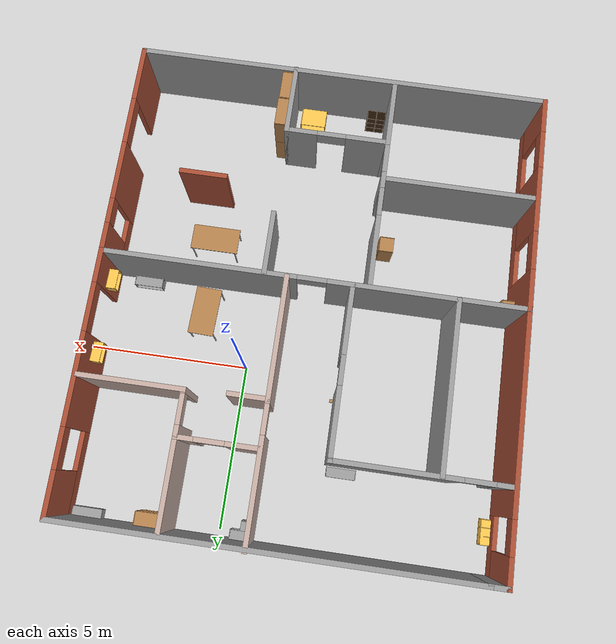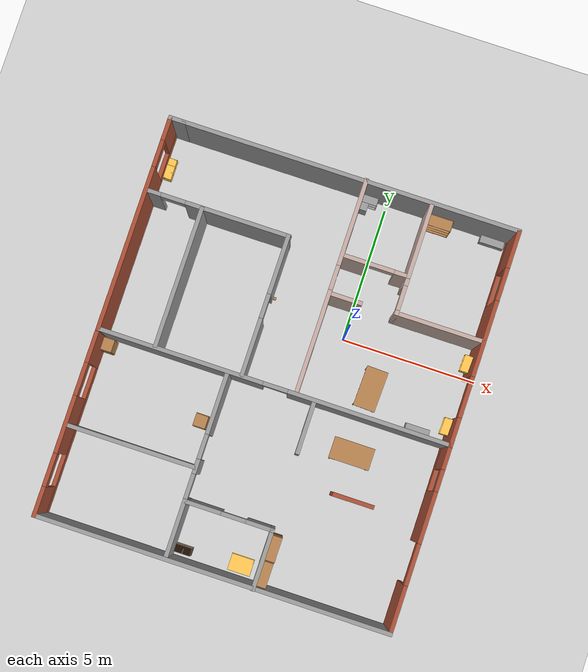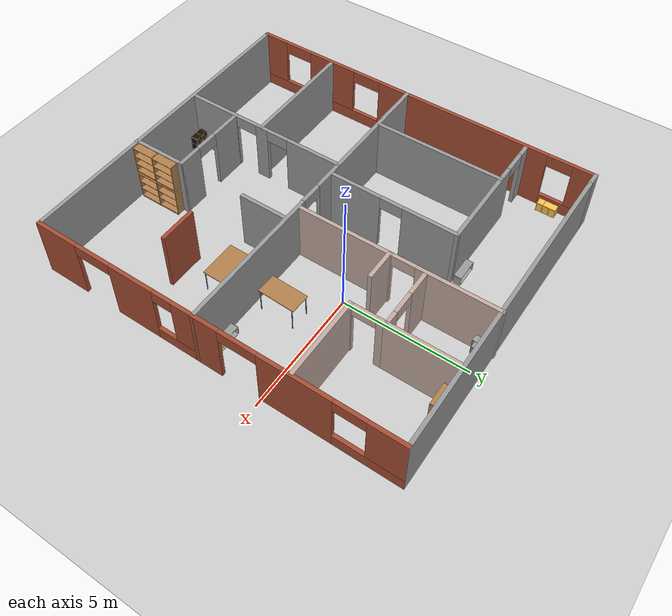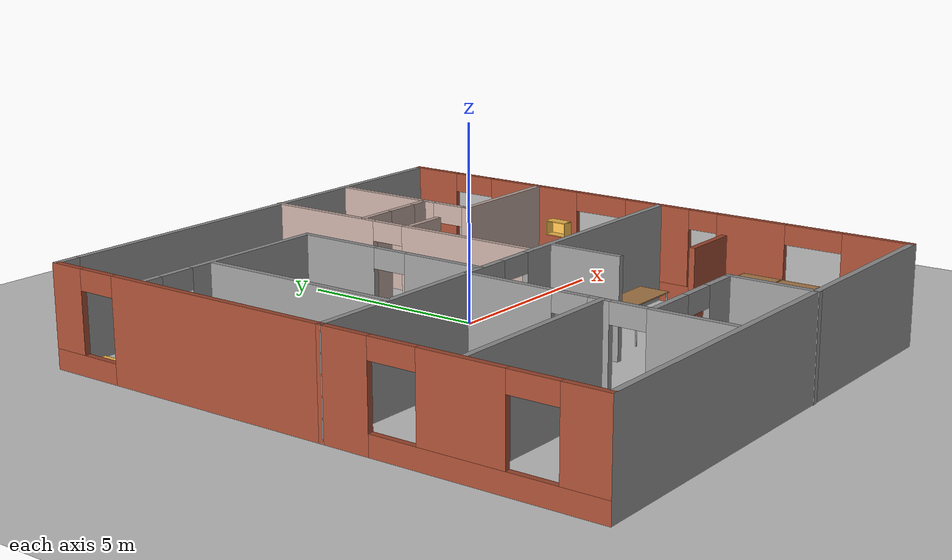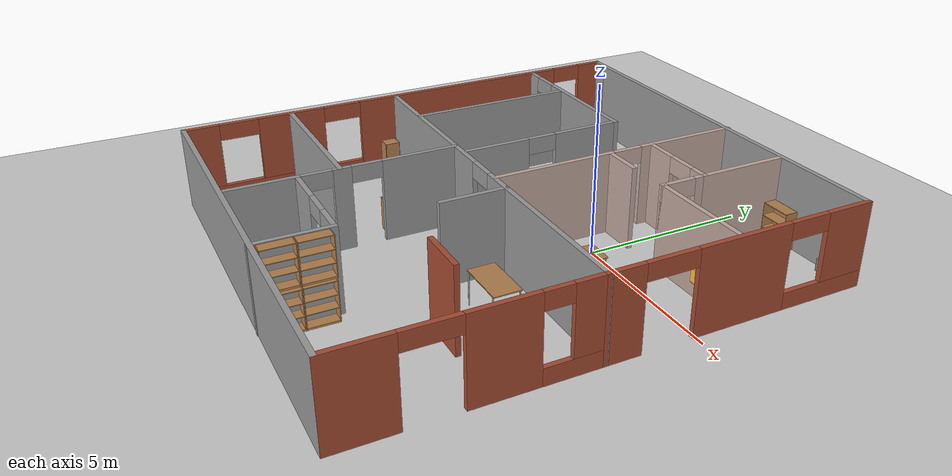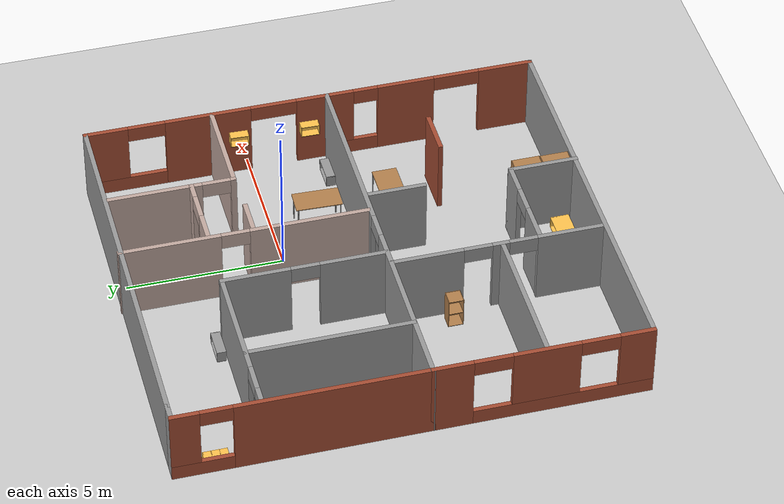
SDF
<sdf version="1.6">
 <world name="default">
  <plugin name="welcome_message" filename="libwelcome_message.so"/>
  <light name="sun" type="directional">
   <pose>0 0 10 0 -0 0</pose>
   <diffuse>0.8 0.8 0.8 1</diffuse>
   <specular>0.2 0.2 0.2 1</specular>
   <attenuation>
    <range>1000</range>
    <constant>0.9</constant>
    <linear>0.01</linear>
    <quadratic>0.001</quadratic>
   </attenuation>
   <direction>-0.5 0.1 -0.9</direction>
  </light>
  <model name="ground_plane">
   <static>1</static>
   <link name="link">
    <collision name="collision">
     <geometry><plane><normal>0 0 1</normal><size>100 100</size></plane></geometry>
     <surface>
      <contact><collide_bitmask>65535</collide_bitmask></contact>
      <friction><ode><mu>100</mu><mu2>50</mu2></ode></friction>
     </surface>
    </collision>
    <visual name="visual">
     <cast_shadows>0</cast_shadows>
     <geometry><plane><normal>0 0 1</normal><size>100 100</size></plane></geometry>
     <material>
      <script><uri>file://media/materials/scripts/gazebo.material</uri><name>Gazebo/Grey</name></script>
     </material>
    </visual>
   </link>
  </model>
  <gravity>0 0 -9.8</gravity>
  <magnetic_field>6e-06 2.3e-05 -4.2e-05</magnetic_field>
  <atmosphere type="adiabatic"/>
  <physics name="default_physics" default="0" type="ode">
   <max_step_size>0.001</max_step_size>
   <real_time_factor>1</real_time_factor>
   <real_time_update_rate>1000</real_time_update_rate>
  </physics>
  <scene><ambient>0.4 0.4 0.4 1</ambient><background>0.7 0.7 0.7 1</background><shadows>1</shadows></scene>
  <spherical_coordinates>
   <surface_model>EARTH_WGS84</surface_model>
   <latitude_deg>0</latitude_deg>
   <longitude_deg>0</longitude_deg>
   <elevation>0</elevation>
   <heading_deg>0</heading_deg>
  </spherical_coordinates>
  <model name="floor_plan">
   <pose>-1.7957 -2.03382 -0.009377 0 -0 0</pose>
   <link name="Wall_0">
    <pose>0 -0.539534 0 0 -0 3.14039</pose>
    <visual name="Wall_0_Visual_0">
     <pose>-3.50083 0 1.25 0 -0 0</pose>
     <geometry><box><size>5.99834 0.15 2.5</size></box></geometry>
     <material>
      <script><uri>file://media/materials/scripts/gazebo.material</uri><name>Gazebo/Grey</name></script>
      <ambient>1 1 1 1</ambient>
     </material>
     <meta><layer>0</layer></meta>
    </visual>
    <collision name="Wall_0_Collision_0">
     <geometry><box><size>5.99834 0.15 2.5</size></box></geometry>
     <pose>-3.50083 0 1.25 0 -0 0</pose>
    </collision>
    <visual name="Wall_0_Visual_1">
     <pose>3.44917 0 1.25 0 -0 0</pose>
     <geometry><box><size>6.10166 0.15 2.5</size></box></geometry>
     <material>
      <script><uri>file://media/materials/scripts/gazebo.material</uri><name>Gazebo/Grey</name></script>
      <ambient>1 1 1 1</ambient>
     </material>
     <meta><layer>0</layer></meta>
    </visual>
    <collision name="Wall_0_Collision_1">
     <geometry><box><size>6.10166 0.15 2.5</size></box></geometry>
     <pose>3.44917 0 1.25 0 -0 0</pose>
    </collision>
    <visual name="Wall_0_Visual_2">
     <pose>-0.051658 0 2.25 0 -0 0</pose>
     <geometry><box><size>0.9 0.15 0.5</size></box></geometry>
     <material>
      <script><uri>file://media/materials/scripts/gazebo.material</uri><name>Gazebo/Grey</name></script>
      <ambient>1 1 1 1</ambient>
     </material>
     <meta><layer>0</layer></meta>
    </visual>
    <collision name="Wall_0_Collision_2">
     <geometry><box><size>0.9 0.15 0.5</size></box></geometry>
     <pose>-0.051658 0 2.25 0 -0 0</pose>
    </collision>
   </link>
   <link name="Wall_11">
    <collision name="Wall_11_Collision">
     <geometry><box><size>2 0.15 2.5</size></box></geometry>
     <pose>0 0 1.25 0 -0 0</pose>
    </collision>
    <visual name="Wall_11_Visual">
     <pose>0 0 1.25 0 -0 0</pose>
     <geometry><box><size>2 0.15 2.5</size></box></geometry>
     <material>
      <script><uri>file://media/materials/scripts/gazebo.material</uri><name>Gazebo/Grey</name></script>
      <ambient>1 1 1 1</ambient>
     </material>
     <meta><layer>0</layer></meta>
    </visual>
    <pose>1.48948 -1.49915 0 0 0 -1.5708</pose>
   </link>
   <link name="Wall_13">
    <collision name="Wall_13_Collision">
     <geometry><box><size>1.5 0.15 2.5</size></box></geometry>
     <pose>0 0 1.25 0 -0 0</pose>
    </collision>
    <visual name="Wall_13_Visual">
     <pose>0 0 1.25 0 -0 0</pose>
     <geometry><box><size>1.5 0.15 2.5</size></box></geometry>
     <material>
      <script><uri>file://media/materials/scripts/gazebo.material</uri><name>Gazebo/Bricks</name></script>
      <ambient>1 1 1 1</ambient>
     </material>
     <meta><layer>0</layer></meta>
    </visual>
    <pose>3.82409 -3.40918 0 0 -0 0</pose>
   </link>
   <link name="Wall_15">
    <collision name="Wall_15_Collision">
     <geometry><box><size>4.75 0.15 2.5</size></box></geometry>
     <pose>0 0 1.25 0 -0 0</pose>
    </collision>
    <visual name="Wall_15_Visual">
     <pose>0 0 1.25 0 -0 0</pose>
     <geometry><box><size>4.75 0.15 2.5</size></box></geometry>
     <material>
      <script><uri>file://media/materials/scripts/gazebo.material</uri><name>Gazebo/Grey</name></script>
      <ambient>1 1 1 1</ambient>
     </material>
     <meta><layer>0</layer></meta>
    </visual>
    <pose>-3.97817 -4.0327 0 0 -0 3.14159</pose>
   </link>
   <link name="Wall_2">
    <pose>-6.42506 -3.93398 0 0 0 -1.5708</pose>
    <visual name="Wall_2_Visual_0">
     <pose>-2.80871 0 1.25 0 -0 0</pose>
     <geometry><box><size>1.30653 0.15 2.5</size></box></geometry>
     <material>
      <script><uri>file://media/materials/scripts/gazebo.material</uri><name>Gazebo/Bricks</name></script>
      <ambient>1 1 1 1</ambient>
     </material>
     <meta><layer>0</layer></meta>
    </visual>
    <collision name="Wall_2_Collision_0">
     <geometry><box><size>1.30653 0.15 2.5</size></box></geometry>
     <pose>-2.80871 0 1.25 0 -0 0</pose>
    </collision>
    <visual name="Wall_2_Visual_1">
     <pose>0.653263 0 0.25 0 -0 0</pose>
     <geometry><box><size>5.61743 0.15 0.5</size></box></geometry>
     <material>
      <script><uri>file://media/materials/scripts/gazebo.material</uri><name>Gazebo/Bricks</name></script>
      <ambient>1 1 1 1</ambient>
     </material>
     <meta><layer>0</layer></meta>
    </visual>
    <collision name="Wall_2_Collision_1">
     <geometry><box><size>5.61743 0.15 0.5</size></box></geometry>
     <pose>0.653263 0 0.25 0 -0 0</pose>
    </collision>
    <visual name="Wall_2_Visual_2">
     <pose>0.095441 0 1.5 0 -0 0</pose>
     <geometry><box><size>2.10179 0.15 2</size></box></geometry>
     <material>
      <script><uri>file://media/materials/scripts/gazebo.material</uri><name>Gazebo/Bricks</name></script>
      <ambient>1 1 1 1</ambient>
     </material>
     <meta><layer>0</layer></meta>
    </visual>
    <collision name="Wall_2_Collision_2">
     <geometry><box><size>2.10179 0.15 2</size></box></geometry>
     <pose>0.095441 0 1.5 0 -0 0</pose>
    </collision>
    <visual name="Wall_2_Visual_3">
     <pose>2.90416 0 1.5 0 -0 0</pose>
     <geometry><box><size>1.11564 0.15 2</size></box></geometry>
     <material>
      <script><uri>file://media/materials/scripts/gazebo.material</uri><name>Gazebo/Bricks</name></script>
      <ambient>1 1 1 1</ambient>
     </material>
     <meta><layer>0</layer></meta>
    </visual>
    <collision name="Wall_2_Collision_3">
     <geometry><box><size>1.11564 0.15 2</size></box></geometry>
     <pose>2.90416 0 1.5 0 -0 0</pose>
    </collision>
    <visual name="Wall_2_Visual_4">
     <pose>-1.55545 0 2.25 0 -0 0</pose>
     <geometry><box><size>1.2 0.15 0.5</size></box></geometry>
     <material>
      <script><uri>file://media/materials/scripts/gazebo.material</uri><name>Gazebo/Bricks</name></script>
      <ambient>1 1 1 1</ambient>
     </material>
     <meta><layer>0</layer></meta>
    </visual>
    <collision name="Wall_2_Collision_4">
     <geometry><box><size>1.2 0.15 0.5</size></box></geometry>
     <pose>-1.55545 0 2.25 0 -0 0</pose>
    </collision>
    <visual name="Wall_2_Visual_5">
     <pose>1.74633 0 2.25 0 -0 0</pose>
     <geometry><box><size>1.2 0.15 0.5</size></box></geometry>
     <material>
      <script><uri>file://media/materials/scripts/gazebo.material</uri><name>Gazebo/Bricks</name></script>
      <ambient>1 1 1 1</ambient>
     </material>
     <meta><layer>0</layer></meta>
    </visual>
    <collision name="Wall_2_Collision_5">
     <geometry><box><size>1.2 0.15 0.5</size></box></geometry>
     <pose>1.74633 0 2.25 0 -0 0</pose>
    </collision>
   </link>
   <link name="Wall_3">
    <collision name="Wall_3_Collision">
     <geometry><box><size>13 0.15 2.5</size></box></geometry>
     <pose>0 0 1.25 0 -0 0</pose>
    </collision>
    <visual name="Wall_3_Visual">
     <pose>0 0 1.25 0 -0 0</pose>
     <geometry><box><size>13 0.15 2.5</size></box></geometry>
     <material>
      <script><uri>file://media/materials/scripts/gazebo.material</uri><name>Gazebo/Grey</name></script>
      <ambient>1 1 1 1</ambient>
     </material>
     <meta><layer>0</layer></meta>
    </visual>
    <pose>0 -7.32112 0 0 0 -2.4e-05</pose>
   </link>
   <link name="Wall_36">
    <pose>-1.17934 2.06051 0 0 -0 1.5708</pose>
    <visual name="Wall_36_Visual_0">
     <pose>-1.55306 0 1.25 0 -0 0</pose>
     <geometry><box><size>2.14389 0.15 2.5</size></box></geometry>
     <material>
      <script><uri>file://media/materials/scripts/gazebo.material</uri><name>Gazebo/Grey</name></script>
      <ambient>1 1 1 1</ambient>
     </material>
     <meta><layer>0</layer></meta>
    </visual>
    <collision name="Wall_36_Collision_0">
     <geometry><box><size>2.14389 0.15 2.5</size></box></geometry>
     <pose>-1.55306 0 1.25 0 -0 0</pose>
    </collision>
    <visual name="Wall_36_Visual_1">
     <pose>1.52195 0 1.25 0 -0 0</pose>
     <geometry><box><size>2.20611 0.15 2.5</size></box></geometry>
     <material>
      <script><uri>file://media/materials/scripts/gazebo.material</uri><name>Gazebo/Grey</name></script>
      <ambient>1 1 1 1</ambient>
     </material>
     <meta><layer>0</layer></meta>
    </visual>
    <collision name="Wall_36_Collision_1">
     <geometry><box><size>2.20611 0.15 2.5</size></box></geometry>
     <pose>1.52195 0 1.25 0 -0 0</pose>
    </collision>
    <visual name="Wall_36_Visual_2">
     <pose>-0.031111 0 2.25 0 -0 0</pose>
     <geometry><box><size>0.9 0.15 0.5</size></box></geometry>
     <material>
      <script><uri>file://media/materials/scripts/gazebo.material</uri><name>Gazebo/Grey</name></script>
      <ambient>1 1 1 1</ambient>
     </material>
     <meta><layer>0</layer></meta>
    </visual>
    <collision name="Wall_36_Collision_2">
     <geometry><box><size>0.9 0.15 0.5</size></box></geometry>
     <pose>-0.031111 0 2.25 0 -0 0</pose>
    </collision>
   </link>
   <link name="Wall_37">
    <pose>-3.72933 4.61051 0 0 -0 3.14159</pose>
    <visual name="Wall_37_Visual_0">
     <pose>-0.694741 0 1.25 0 -0 0</pose>
     <geometry><box><size>3.86052 0.15 2.5</size></box></geometry>
     <material>
      <script><uri>file://media/materials/scripts/gazebo.material</uri><name>Gazebo/Grey</name></script>
      <ambient>1 1 1 1</ambient>
     </material>
     <meta><layer>0</layer></meta>
    </visual>
    <collision name="Wall_37_Collision_0">
     <geometry><box><size>3.86052 0.15 2.5</size></box></geometry>
     <pose>-0.694741 0 1.25 0 -0 0</pose>
    </collision>
    <visual name="Wall_37_Visual_1">
     <pose>2.38026 0 1.25 0 -0 0</pose>
     <geometry><box><size>0.489482 0.15 2.5</size></box></geometry>
     <material>
      <script><uri>file://media/materials/scripts/gazebo.material</uri><name>Gazebo/Grey</name></script>
      <ambient>1 1 1 1</ambient>
     </material>
     <meta><layer>0</layer></meta>
    </visual>
    <collision name="Wall_37_Collision_1">
     <geometry><box><size>0.489482 0.15 2.5</size></box></geometry>
     <pose>2.38026 0 1.25 0 -0 0</pose>
    </collision>
    <visual name="Wall_37_Visual_2">
     <pose>1.68552 0 2.25 0 -0 0</pose>
     <geometry><box><size>0.9 0.15 0.5</size></box></geometry>
     <material>
      <script><uri>file://media/materials/scripts/gazebo.material</uri><name>Gazebo/Grey</name></script>
      <ambient>1 1 1 1</ambient>
     </material>
     <meta><layer>0</layer></meta>
    </visual>
    <collision name="Wall_37_Collision_2">
     <geometry><box><size>0.9 0.15 0.5</size></box></geometry>
     <pose>1.68552 0 2.25 0 -0 0</pose>
    </collision>
   </link>
   <link name="Wall_39">
    <collision name="Wall_39_Collision">
     <geometry><box><size>5.25 0.15 2.5</size></box></geometry>
     <pose>0 0 1.25 0 -0 0</pose>
    </collision>
    <visual name="Wall_39_Visual">
     <pose>0 0 1.25 0 -0 0</pose>
     <geometry><box><size>5.25 0.15 2.5</size></box></geometry>
     <material>
      <script><uri>file://media/materials/scripts/gazebo.material</uri><name>Gazebo/Grey</name></script>
      <ambient>1 1 1 1</ambient>
     </material>
     <meta><layer>0</layer></meta>
    </visual>
    <pose>-4.34796 2.03294 0 0 0 -1.5708</pose>
   </link>
   <link name="Wall_4">
    <pose>6.42506 -3.93427 0 0 -0 1.5708</pose>
    <visual name="Wall_4_Visual_0">
     <pose>-2.56147 0 1.25 0 -0 0</pose>
     <geometry><box><size>1.80105 0.15 2.5</size></box></geometry>
     <material>
      <script><uri>file://media/materials/scripts/gazebo.material</uri><name>Gazebo/Bricks</name></script>
      <ambient>1 1 1 1</ambient>
     </material>
     <meta><layer>0</layer></meta>
    </visual>
    <collision name="Wall_4_Collision_0">
     <geometry><box><size>1.80105 0.15 2.5</size></box></geometry>
     <pose>-2.56147 0 1.25 0 -0 0</pose>
    </collision>
    <visual name="Wall_4_Visual_1">
     <pose>0.775723 0 1.25 0 -0 0</pose>
     <geometry><box><size>1.87334 0.15 2.5</size></box></geometry>
     <material>
      <script><uri>file://media/materials/scripts/gazebo.material</uri><name>Gazebo/Bricks</name></script>
      <ambient>1 1 1 1</ambient>
     </material>
     <meta><layer>0</layer></meta>
    </visual>
    <collision name="Wall_4_Collision_1">
     <geometry><box><size>1.87334 0.15 2.5</size></box></geometry>
     <pose>0.775723 0 1.25 0 -0 0</pose>
    </collision>
    <visual name="Wall_4_Visual_2">
     <pose>2.5872 0 0.25 0 -0 0</pose>
     <geometry><box><size>1.74961 0.15 0.5</size></box></geometry>
     <material>
      <script><uri>file://media/materials/scripts/gazebo.material</uri><name>Gazebo/Bricks</name></script>
      <ambient>1 1 1 1</ambient>
     </material>
     <meta><layer>0</layer></meta>
    </visual>
    <collision name="Wall_4_Collision_2">
     <geometry><box><size>1.74961 0.15 0.5</size></box></geometry>
     <pose>2.5872 0 0.25 0 -0 0</pose>
    </collision>
    <visual name="Wall_4_Visual_3">
     <pose>2.9872 0 1.5 0 -0 0</pose>
     <geometry><box><size>0.949605 0.15 2</size></box></geometry>
     <material>
      <script><uri>file://media/materials/scripts/gazebo.material</uri><name>Gazebo/Bricks</name></script>
      <ambient>1 1 1 1</ambient>
     </material>
     <meta><layer>0</layer></meta>
    </visual>
    <collision name="Wall_4_Collision_3">
     <geometry><box><size>0.949605 0.15 2</size></box></geometry>
     <pose>2.9872 0 1.5 0 -0 0</pose>
    </collision>
    <visual name="Wall_4_Visual_4">
     <pose>-0.910948 0 2.25 0 -0 0</pose>
     <geometry><box><size>1.5 0.15 0.5</size></box></geometry>
     <material>
      <script><uri>file://media/materials/scripts/gazebo.material</uri><name>Gazebo/Bricks</name></script>
      <ambient>1 1 1 1</ambient>
     </material>
     <meta><layer>0</layer></meta>
    </visual>
    <collision name="Wall_4_Collision_4">
     <geometry><box><size>1.5 0.15 0.5</size></box></geometry>
     <pose>-0.910948 0 2.25 0 -0 0</pose>
    </collision>
    <visual name="Wall_4_Visual_5">
     <pose>2.11239 0 2.25 0 -0 0</pose>
     <geometry><box><size>0.8 0.15 0.5</size></box></geometry>
     <material>
      <script><uri>file://media/materials/scripts/gazebo.material</uri><name>Gazebo/Bricks</name></script>
      <ambient>1 1 1 1</ambient>
     </material>
     <meta><layer>0</layer></meta>
    </visual>
    <collision name="Wall_4_Collision_5">
     <geometry><box><size>0.8 0.15 0.5</size></box></geometry>
     <pose>2.11239 0 2.25 0 -0 0</pose>
    </collision>
   </link>
   <link name="Wall_45">
    <pose>6.425 3.37786 0 0 -0 1.57081</pose>
    <visual name="Wall_45_Visual_0">
     <pose>-3.45923 0 1.25 0 -0 0</pose>
     <geometry><box><size>1.08155 0.15 2.5</size></box></geometry>
     <material>
      <script><uri>file://media/materials/scripts/gazebo.material</uri><name>Gazebo/Bricks</name></script>
      <ambient>1 1 1 1</ambient>
     </material>
     <meta><layer>0</layer></meta>
    </visual>
    <collision name="Wall_45_Collision_0">
     <geometry><box><size>1.08155 0.15 2.5</size></box></geometry>
     <pose>-3.45923 0 1.25 0 -0 0</pose>
    </collision>
    <visual name="Wall_45_Visual_1">
     <pose>-0.023066 0 1.25 0 -0 0</pose>
     <geometry><box><size>2.79077 0.15 2.5</size></box></geometry>
     <material>
      <script><uri>file://media/materials/scripts/gazebo.material</uri><name>Gazebo/Bricks</name></script>
      <ambient>1 1 1 1</ambient>
     </material>
     <meta><layer>0</layer></meta>
    </visual>
    <collision name="Wall_45_Collision_1">
     <geometry><box><size>2.79077 0.15 2.5</size></box></geometry>
     <pose>-0.023066 0 1.25 0 -0 0</pose>
    </collision>
    <visual name="Wall_45_Visual_2">
     <pose>2.68616 0 0.25 0 -0 0</pose>
     <geometry><box><size>2.62768 0.15 0.5</size></box></geometry>
     <material>
      <script><uri>file://media/materials/scripts/gazebo.material</uri><name>Gazebo/Bricks</name></script>
      <ambient>1 1 1 1</ambient>
     </material>
     <meta><layer>0</layer></meta>
    </visual>
    <collision name="Wall_45_Collision_2">
     <geometry><box><size>2.62768 0.15 0.5</size></box></geometry>
     <pose>2.68616 0 0.25 0 -0 0</pose>
    </collision>
    <visual name="Wall_45_Visual_3">
     <pose>3.28616 0 1.5 0 -0 0</pose>
     <geometry><box><size>1.42768 0.15 2</size></box></geometry>
     <material>
      <script><uri>file://media/materials/scripts/gazebo.material</uri><name>Gazebo/Bricks</name></script>
      <ambient>1 1 1 1</ambient>
     </material>
     <meta><layer>0</layer></meta>
    </visual>
    <collision name="Wall_45_Collision_3">
     <geometry><box><size>1.42768 0.15 2</size></box></geometry>
     <pose>3.28616 0 1.5 0 -0 0</pose>
    </collision>
    <visual name="Wall_45_Visual_4">
     <pose>-2.16845 0 2.25 0 -0 0</pose>
     <geometry><box><size>1.5 0.15 0.5</size></box></geometry>
     <material>
      <script><uri>file://media/materials/scripts/gazebo.material</uri><name>Gazebo/Bricks</name></script>
      <ambient>1 1 1 1</ambient>
     </material>
     <meta><layer>0</layer></meta>
    </visual>
    <collision name="Wall_45_Collision_4">
     <geometry><box><size>1.5 0.15 0.5</size></box></geometry>
     <pose>-2.16845 0 2.25 0 -0 0</pose>
    </collision>
    <visual name="Wall_45_Visual_5">
     <pose>1.97232 0 2.25 0 -0 0</pose>
     <geometry><box><size>1.2 0.15 0.5</size></box></geometry>
     <material>
      <script><uri>file://media/materials/scripts/gazebo.material</uri><name>Gazebo/Bricks</name></script>
      <ambient>1 1 1 1</ambient>
     </material>
     <meta><layer>0</layer></meta>
    </visual>
    <collision name="Wall_45_Collision_5">
     <geometry><box><size>1.2 0.15 0.5</size></box></geometry>
     <pose>1.97232 0 2.25 0 -0 0</pose>
    </collision>
   </link>
   <link name="Wall_46">
    <collision name="Wall_46_Collision">
     <geometry><box><size>12.5 0.15 2.5</size></box></geometry>
     <pose>0 0 1.25 0 -0 0</pose>
    </collision>
    <visual name="Wall_46_Visual">
     <pose>0 0 1.25 0 -0 0</pose>
     <geometry><box><size>12.5 0.15 2.5</size></box></geometry>
     <material>
      <script><uri>file://media/materials/scripts/gazebo.material</uri><name>Gazebo/Grey</name></script>
      <ambient>1 1 1 1</ambient>
     </material>
     <meta><layer>0</layer></meta>
    </visual>
    <pose>0.249944 7.303 0 0 -0 3.14159</pose>
   </link>
   <link name="Wall_48">
    <pose>-6.42506 3.378 0 0 -0 1.5708</pose>
    <visual name="Wall_48_Visual_0">
     <pose>-0.956686 0 1.25 0 -0 0</pose>
     <geometry><box><size>6.08663 0.15 2.5</size></box></geometry>
     <material>
      <script><uri>file://media/materials/scripts/gazebo.material</uri><name>Gazebo/Bricks</name></script>
      <ambient>1 1 1 1</ambient>
     </material>
     <meta><layer>0</layer></meta>
    </visual>
    <collision name="Wall_48_Collision_0">
     <geometry><box><size>6.08663 0.15 2.5</size></box></geometry>
     <pose>-0.956686 0 1.25 0 -0 0</pose>
    </collision>
    <visual name="Wall_48_Visual_1">
     <pose>3.04331 0 0.25 0 -0 0</pose>
     <geometry><box><size>1.91337 0.15 0.5</size></box></geometry>
     <material>
      <script><uri>file://media/materials/scripts/gazebo.material</uri><name>Gazebo/Bricks</name></script>
      <ambient>1 1 1 1</ambient>
     </material>
     <meta><layer>0</layer></meta>
    </visual>
    <collision name="Wall_48_Collision_1">
     <geometry><box><size>1.91337 0.15 0.5</size></box></geometry>
     <pose>3.04331 0 0.25 0 -0 0</pose>
    </collision>
    <visual name="Wall_48_Visual_2">
     <pose>3.54331 0 1.5 0 -0 0</pose>
     <geometry><box><size>0.913372 0.15 2</size></box></geometry>
     <material>
      <script><uri>file://media/materials/scripts/gazebo.material</uri><name>Gazebo/Bricks</name></script>
      <ambient>1 1 1 1</ambient>
     </material>
     <meta><layer>0</layer></meta>
    </visual>
    <collision name="Wall_48_Collision_2">
     <geometry><box><size>0.913372 0.15 2</size></box></geometry>
     <pose>3.54331 0 1.5 0 -0 0</pose>
    </collision>
    <visual name="Wall_48_Visual_3">
     <pose>2.58663 0 2.25 0 -0 0</pose>
     <geometry><box><size>1 0.15 0.5</size></box></geometry>
     <material>
      <script><uri>file://media/materials/scripts/gazebo.material</uri><name>Gazebo/Bricks</name></script>
      <ambient>1 1 1 1</ambient>
     </material>
     <meta><layer>0</layer></meta>
    </visual>
    <collision name="Wall_48_Collision_3">
     <geometry><box><size>1 0.15 0.5</size></box></geometry>
     <pose>2.58663 0 2.25 0 -0 0</pose>
    </collision>
   </link>
   <link name="Wall_49">
    <collision name="Wall_49_Collision">
     <geometry><box><size>0.65 0.15 2.5</size></box></geometry>
     <pose>0 0 1.25 0 -0 0</pose>
    </collision>
    <visual name="Wall_49_Visual">
     <pose>0 0 1.25 0 -0 0</pose>
     <geometry><box><size>0.65 0.15 2.5</size></box></geometry>
     <material>
      <script><uri>file://media/materials/scripts/gazebo.material</uri><name>Gazebo/Grey</name></script>
      <ambient>1 1 1 1</ambient>
     </material>
     <meta><layer>0</layer></meta>
    </visual>
    <pose>-6.17506 7.303 0 0 -0 0</pose>
   </link>
   <link name="Wall_51">
    <pose>0.800151 3.41451 0 0 -0 1.5708</pose>
    <visual name="Wall_51_Visual_0">
     <pose>-2.06358 0 1.25 0 -0 0</pose>
     <geometry><box><size>3.87284 0.15 2.5</size></box></geometry>
     <material>
      <script><uri>file://media/materials/scripts/gazebo.material</uri><name>Gazebo/Grey</name></script>
      <ambient>0.760784 0.662745 0.627451 1</ambient>
     </material>
     <meta><layer>0</layer></meta>
    </visual>
    <collision name="Wall_51_Collision_0">
     <geometry><box><size>3.87284 0.15 2.5</size></box></geometry>
     <pose>-2.06358 0 1.25 0 -0 0</pose>
    </collision>
    <visual name="Wall_51_Visual_1">
     <pose>2.38642 0 1.25 0 -0 0</pose>
     <geometry><box><size>3.22716 0.15 2.5</size></box></geometry>
     <material>
      <script><uri>file://media/materials/scripts/gazebo.material</uri><name>Gazebo/Grey</name></script>
      <ambient>0.760784 0.662745 0.627451 1</ambient>
     </material>
     <meta><layer>0</layer></meta>
    </visual>
    <collision name="Wall_51_Collision_1">
     <geometry><box><size>3.22716 0.15 2.5</size></box></geometry>
     <pose>2.38642 0 1.25 0 -0 0</pose>
    </collision>
    <visual name="Wall_51_Visual_2">
     <pose>0.322836 0 2.25 0 -0 0</pose>
     <geometry><box><size>0.9 0.15 0.5</size></box></geometry>
     <material>
      <script><uri>file://media/materials/scripts/gazebo.material</uri><name>Gazebo/Grey</name></script>
      <ambient>0.760784 0.662745 0.627451 1</ambient>
     </material>
     <meta><layer>0</layer></meta>
    </visual>
    <collision name="Wall_51_Collision_2">
     <geometry><box><size>0.9 0.15 0.5</size></box></geometry>
     <pose>0.322836 0 2.25 0 -0 0</pose>
    </collision>
   </link>
   <link name="Wall_53">
    <pose>2.06768 4.57778 0 0 -0 0</pose>
    <visual name="Wall_53_Visual_0">
     <pose>-0.747106 0 1.25 0 -0 0</pose>
     <geometry><box><size>1.00579 0.15 2.5</size></box></geometry>
     <material>
      <script><uri>file://media/materials/scripts/gazebo.material</uri><name>Gazebo/Grey</name></script>
      <ambient>0.760784 0.662745 0.627451 1</ambient>
     </material>
     <meta><layer>0</layer></meta>
    </visual>
    <collision name="Wall_53_Collision_0">
     <geometry><box><size>1.00579 0.15 2.5</size></box></geometry>
     <pose>-0.747106 0 1.25 0 -0 0</pose>
    </collision>
    <visual name="Wall_53_Visual_1">
     <pose>0.952894 0 1.25 0 -0 0</pose>
     <geometry><box><size>0.594213 0.15 2.5</size></box></geometry>
     <material>
      <script><uri>file://media/materials/scripts/gazebo.material</uri><name>Gazebo/Grey</name></script>
      <ambient>0.760784 0.662745 0.627451 1</ambient>
     </material>
     <meta><layer>0</layer></meta>
    </visual>
    <collision name="Wall_53_Collision_1">
     <geometry><box><size>0.594213 0.15 2.5</size></box></geometry>
     <pose>0.952894 0 1.25 0 -0 0</pose>
    </collision>
    <visual name="Wall_53_Visual_2">
     <pose>0.205787 0 2.25 0 -0 0</pose>
     <geometry><box><size>0.9 0.15 0.5</size></box></geometry>
     <material>
      <script><uri>file://media/materials/scripts/gazebo.material</uri><name>Gazebo/Grey</name></script>
      <ambient>0.760784 0.662745 0.627451 1</ambient>
     </material>
     <meta><layer>0</layer></meta>
    </visual>
    <collision name="Wall_53_Collision_2">
     <geometry><box><size>0.9 0.15 0.5</size></box></geometry>
     <pose>0.205787 0 2.25 0 -0 0</pose>
    </collision>
   </link>
   <link name="Wall_54">
    <collision name="Wall_54_Collision">
     <geometry><box><size>2.75 0.15 2.5</size></box></geometry>
     <pose>0 0 1.25 0 -0 0</pose>
    </collision>
    <visual name="Wall_54_Visual">
     <pose>0 0 1.25 0 -0 0</pose>
     <geometry><box><size>2.75 0.15 2.5</size></box></geometry>
     <material>
      <script><uri>file://media/materials/scripts/gazebo.material</uri><name>Gazebo/Grey</name></script>
      <ambient>0.760784 0.662745 0.627451 1</ambient>
     </material>
     <meta><layer>0</layer></meta>
    </visual>
    <pose>3.24268 5.87778 0 0 -0 1.5708</pose>
   </link>
   <link name="Wall_56">
    <pose>3.24268 3.90278 0 0 0 -1.5708</pose>
    <visual name="Wall_56_Visual_0">
     <pose>-0.543058 0 1.25 0 -0 0</pose>
     <geometry><box><size>0.413884 0.15 2.5</size></box></geometry>
     <material>
      <script><uri>file://media/materials/scripts/gazebo.material</uri><name>Gazebo/Grey</name></script>
      <ambient>0.760784 0.662745 0.627451 1</ambient>
     </material>
     <meta><layer>0</layer></meta>
    </visual>
    <collision name="Wall_56_Collision_0">
     <geometry><box><size>0.413884 0.15 2.5</size></box></geometry>
     <pose>-0.543058 0 1.25 0 -0 0</pose>
    </collision>
    <visual name="Wall_56_Visual_1">
     <pose>0.656942 0 1.25 0 -0 0</pose>
     <geometry><box><size>0.186116 0.15 2.5</size></box></geometry>
     <material>
      <script><uri>file://media/materials/scripts/gazebo.material</uri><name>Gazebo/Grey</name></script>
      <ambient>0.760784 0.662745 0.627451 1</ambient>
     </material>
     <meta><layer>0</layer></meta>
    </visual>
    <collision name="Wall_56_Collision_1">
     <geometry><box><size>0.186116 0.15 2.5</size></box></geometry>
     <pose>0.656942 0 1.25 0 -0 0</pose>
    </collision>
    <visual name="Wall_56_Visual_2">
     <pose>0.113884 0 2.25 0 -0 0</pose>
     <geometry><box><size>0.9 0.15 0.5</size></box></geometry>
     <material>
      <script><uri>file://media/materials/scripts/gazebo.material</uri><name>Gazebo/Grey</name></script>
      <ambient>0.760784 0.662745 0.627451 1</ambient>
     </material>
     <meta><layer>0</layer></meta>
    </visual>
    <collision name="Wall_56_Collision_2">
     <geometry><box><size>0.9 0.15 0.5</size></box></geometry>
     <pose>0.113884 0 2.25 0 -0 0</pose>
    </collision>
   </link>
   <link name="Wall_57">
    <collision name="Wall_57_Collision">
     <geometry><box><size>3.25 0.15 2.5</size></box></geometry>
     <pose>0 0 1.25 0 -0 0</pose>
    </collision>
    <visual name="Wall_57_Visual">
     <pose>0 0 1.25 0 -0 0</pose>
     <geometry><box><size>3.25 0.15 2.5</size></box></geometry>
     <material>
      <script><uri>file://media/materials/scripts/gazebo.material</uri><name>Gazebo/Grey</name></script>
      <ambient>0.760784 0.662745 0.627451 1</ambient>
     </material>
     <meta><layer>0</layer></meta>
    </visual>
    <pose>4.79268 3.22778 0 0 -0 0</pose>
   </link>
   <link name="Wall_59">
    <collision name="Wall_59_Collision">
     <geometry><box><size>1.25 0.15 2.5</size></box></geometry>
     <pose>0 0 1.25 0 -0 0</pose>
    </collision>
    <visual name="Wall_59_Visual">
     <pose>0 0 1.25 0 -0 0</pose>
     <geometry><box><size>1.25 0.15 2.5</size></box></geometry>
     <material>
      <script><uri>file://media/materials/scripts/gazebo.material</uri><name>Gazebo/Grey</name></script>
      <ambient>0.760784 0.662745 0.627451 1</ambient>
     </material>
     <meta><layer>0</layer></meta>
    </visual>
    <pose>1.382 3.16183 0 0 -0 0</pose>
   </link>
   <link name="Wall_6">
    <pose>-1.67816 -3.87415 0 0 0 -1.5708</pose>
    <visual name="Wall_6_Visual_0">
     <pose>-2.21563 0 1.25 0 -0 0</pose>
     <geometry><box><size>2.31875 0.15 2.5</size></box></geometry>
     <material>
      <script><uri>file://media/materials/scripts/gazebo.material</uri><name>Gazebo/Grey</name></script>
      <ambient>1 1 1 1</ambient>
     </material>
     <meta><layer>0</layer></meta>
    </visual>
    <collision name="Wall_6_Collision_0">
     <geometry><box><size>2.31875 0.15 2.5</size></box></geometry>
     <pose>-2.21563 0 1.25 0 -0 0</pose>
    </collision>
    <visual name="Wall_6_Visual_1">
     <pose>0.110792 0 1.25 0 -0 0</pose>
     <geometry><box><size>0.534083 0.15 2.5</size></box></geometry>
     <material>
      <script><uri>file://media/materials/scripts/gazebo.material</uri><name>Gazebo/Grey</name></script>
      <ambient>1 1 1 1</ambient>
     </material>
     <meta><layer>0</layer></meta>
    </visual>
    <collision name="Wall_6_Collision_1">
     <geometry><box><size>0.534083 0.15 2.5</size></box></geometry>
     <pose>0.110792 0 1.25 0 -0 0</pose>
    </collision>
    <visual name="Wall_6_Visual_2">
     <pose>2.32642 0 1.25 0 -0 0</pose>
     <geometry><box><size>2.09717 0.15 2.5</size></box></geometry>
     <material>
      <script><uri>file://media/materials/scripts/gazebo.material</uri><name>Gazebo/Grey</name></script>
      <ambient>1 1 1 1</ambient>
     </material>
     <meta><layer>0</layer></meta>
    </visual>
    <collision name="Wall_6_Collision_2">
     <geometry><box><size>2.09717 0.15 2.5</size></box></geometry>
     <pose>2.32642 0 1.25 0 -0 0</pose>
    </collision>
    <visual name="Wall_6_Visual_3">
     <pose>-0.60625 0 2.25 0 -0 0</pose>
     <geometry><box><size>0.9 0.15 0.5</size></box></geometry>
     <material>
      <script><uri>file://media/materials/scripts/gazebo.material</uri><name>Gazebo/Grey</name></script>
      <ambient>1 1 1 1</ambient>
     </material>
     <meta><layer>0</layer></meta>
    </visual>
    <collision name="Wall_6_Collision_3">
     <geometry><box><size>0.9 0.15 0.5</size></box></geometry>
     <pose>-0.60625 0 2.25 0 -0 0</pose>
    </collision>
    <visual name="Wall_6_Visual_4">
     <pose>0.827833 0 2.25 0 -0 0</pose>
     <geometry><box><size>0.9 0.15 0.5</size></box></geometry>
     <material>
      <script><uri>file://media/materials/scripts/gazebo.material</uri><name>Gazebo/Grey</name></script>
      <ambient>1 1 1 1</ambient>
     </material>
     <meta><layer>0</layer></meta>
    </visual>
    <collision name="Wall_6_Collision_4">
     <geometry><box><size>0.9 0.15 0.5</size></box></geometry>
     <pose>0.827833 0 2.25 0 -0 0</pose>
    </collision>
   </link>
   <link name="Wall_8">
    <pose>-0.047711 -5.23951 0 0 -0 0</pose>
    <visual name="Wall_8_Visual_0">
     <pose>-0.96773 0 1.25 0 -0 0</pose>
     <geometry><box><size>1.31454 0.15 2.5</size></box></geometry>
     <material>
      <script><uri>file://media/materials/scripts/gazebo.material</uri><name>Gazebo/Grey</name></script>
      <ambient>1 1 1 1</ambient>
     </material>
     <meta><layer>0</layer></meta>
    </visual>
    <collision name="Wall_8_Collision_0">
     <geometry><box><size>1.31454 0.15 2.5</size></box></geometry>
     <pose>-0.96773 0 1.25 0 -0 0</pose>
    </collision>
    <visual name="Wall_8_Visual_1">
     <pose>1.10727 0 1.25 0 -0 0</pose>
     <geometry><box><size>1.03546 0.15 2.5</size></box></geometry>
     <material>
      <script><uri>file://media/materials/scripts/gazebo.material</uri><name>Gazebo/Grey</name></script>
      <ambient>1 1 1 1</ambient>
     </material>
     <meta><layer>0</layer></meta>
    </visual>
    <collision name="Wall_8_Collision_1">
     <geometry><box><size>1.03546 0.15 2.5</size></box></geometry>
     <pose>1.10727 0 1.25 0 -0 0</pose>
    </collision>
    <visual name="Wall_8_Visual_2">
     <pose>0.13954 0 2.25 0 -0 0</pose>
     <geometry><box><size>0.9 0.15 0.5</size></box></geometry>
     <material>
      <script><uri>file://media/materials/scripts/gazebo.material</uri><name>Gazebo/Grey</name></script>
      <ambient>1 1 1 1</ambient>
     </material>
     <meta><layer>0</layer></meta>
    </visual>
    <collision name="Wall_8_Collision_2">
     <geometry><box><size>0.9 0.15 0.5</size></box></geometry>
     <pose>0.13954 0 2.25 0 -0 0</pose>
    </collision>
   </link>
   <link name="Wall_9">
    <collision name="Wall_9_Collision">
     <geometry><box><size>2.25 0.15 2.5</size></box></geometry>
     <pose>0 0 1.25 0 -0 0</pose>
    </collision>
    <visual name="Wall_9_Visual">
     <pose>0 0 1.25 0 -0 0</pose>
     <geometry><box><size>2.25 0.15 2.5</size></box></geometry>
     <material>
      <script><uri>file://media/materials/scripts/gazebo.material</uri><name>Gazebo/Grey</name></script>
      <ambient>1 1 1 1</ambient>
     </material>
     <meta><layer>0</layer></meta>
    </visual>
    <pose>1.50229 -6.28951 0 0 0 -1.5708</pose>
   </link>
   <static>1</static>
  </model>
  <model name="bookshelf_clone">
   <static>1</static>
   <link name="link">
    <inertial><mass>1</mass></inertial>
    <collision name="back">
     <pose>0 0.005 0.6 0 -0 0</pose>
     <geometry><box><size>0.9 0.01 1.2</size></box></geometry>
    </collision>
    <visual name="visual1">
     <pose>0 0.005 0.6 0 -0 0</pose>
     <geometry><box><size>0.9 0.01 1.2</size></box></geometry>
     <material>
      <script><uri>file://media/materials/scripts/gazebo.material</uri><name>Gazebo/Wood</name></script>
     </material>
    </visual>
    <collision name="left_side">
     <pose>0.45 -0.195 0.6 0 -0 0</pose>
     <geometry><box><size>0.02 0.4 1.2</size></box></geometry>
    </collision>
    <visual name="visual2">
     <pose>0.45 -0.195 0.6 0 -0 0</pose>
     <geometry><box><size>0.02 0.4 1.2</size></box></geometry>
     <material>
      <script><uri>file://media/materials/scripts/gazebo.material</uri><name>Gazebo/Wood</name></script>
     </material>
    </visual>
    <collision name="right_side">
     <pose>-0.45 -0.195 0.6 0 -0 0</pose>
     <geometry><box><size>0.02 0.4 1.2</size></box></geometry>
    </collision>
    <visual name="visual3">
     <pose>-0.45 -0.195 0.6 0 -0 0</pose>
     <geometry><box><size>0.02 0.4 1.2</size></box></geometry>
     <material>
      <script><uri>file://media/materials/scripts/gazebo.material</uri><name>Gazebo/Wood</name></script>
     </material>
    </visual>
    <collision name="bottom">
     <pose>0 -0.195 0.03 0 -0 0</pose>
     <geometry><box><size>0.88 0.4 0.06</size></box></geometry>
    </collision>
    <visual name="visual4">
     <pose>0 -0.195 0.03 0 -0 0</pose>
     <geometry><box><size>0.88 0.4 0.06</size></box></geometry>
     <material>
      <script><uri>file://media/materials/scripts/gazebo.material</uri><name>Gazebo/Wood</name></script>
     </material>
    </visual>
    <collision name="top">
     <pose>0 -0.195 1.19 0 -0 0</pose>
     <geometry><box><size>0.88 0.4 0.02</size></box></geometry>
    </collision>
    <visual name="visual5">
     <pose>0 -0.195 1.19 0 -0 0</pose>
     <geometry><box><size>0.88 0.4 0.02</size></box></geometry>
     <material>
      <script><uri>file://media/materials/scripts/gazebo.material</uri><name>Gazebo/Wood</name></script>
     </material>
    </visual>
    <collision name="low_shelf">
     <pose>0 -0.195 0.43 0 -0 0</pose>
     <geometry><box><size>0.88 0.4 0.02</size></box></geometry>
    </collision>
    <visual name="visual6">
     <pose>0 -0.195 0.43 0 -0 0</pose>
     <geometry><box><size>0.88 0.4 0.02</size></box></geometry>
     <material>
      <script><uri>file://media/materials/scripts/gazebo.material</uri><name>Gazebo/Wood</name></script>
     </material>
    </visual>
    <collision name="high_shelf">
     <pose>0 -0.195 0.8 0 -0 0</pose>
     <geometry><box><size>0.88 0.4 0.02</size></box></geometry>
    </collision>
    <visual name="visual7">
     <pose>0 -0.195 0.8 0 -0 0</pose>
     <geometry><box><size>0.88 0.4 0.02</size></box></geometry>
     <material>
      <script><uri>file://media/materials/scripts/gazebo.material</uri><name>Gazebo/Wood</name></script>
     </material>
    </visual>
   </link>
   <pose>-0.27446 -7.87472 0 0 -0 1.5707</pose>
  </model>
  <model name="bookshelf_clone_0">
   <static>1</static>
   <link name="link">
    <inertial><mass>1</mass></inertial>
    <collision name="back">
     <pose>0 0.005 0.6 0 -0 0</pose>
     <geometry><box><size>0.9 0.01 1.2</size></box></geometry>
    </collision>
    <visual name="visual1">
     <pose>0 0.005 0.6 0 -0 0</pose>
     <geometry><box><size>0.9 0.01 1.2</size></box></geometry>
     <material>
      <script><uri>file://media/materials/scripts/gazebo.material</uri><name>Gazebo/Wood</name></script>
     </material>
    </visual>
    <collision name="left_side">
     <pose>0.45 -0.195 0.6 0 -0 0</pose>
     <geometry><box><size>0.02 0.4 1.2</size></box></geometry>
    </collision>
    <visual name="visual2">
     <pose>0.45 -0.195 0.6 0 -0 0</pose>
     <geometry><box><size>0.02 0.4 1.2</size></box></geometry>
     <material>
      <script><uri>file://media/materials/scripts/gazebo.material</uri><name>Gazebo/Wood</name></script>
     </material>
    </visual>
    <collision name="right_side">
     <pose>-0.45 -0.195 0.6 0 -0 0</pose>
     <geometry><box><size>0.02 0.4 1.2</size></box></geometry>
    </collision>
    <visual name="visual3">
     <pose>-0.45 -0.195 0.6 0 -0 0</pose>
     <geometry><box><size>0.02 0.4 1.2</size></box></geometry>
     <material>
      <script><uri>file://media/materials/scripts/gazebo.material</uri><name>Gazebo/Wood</name></script>
     </material>
    </visual>
    <collision name="bottom">
     <pose>0 -0.195 0.03 0 -0 0</pose>
     <geometry><box><size>0.88 0.4 0.06</size></box></geometry>
    </collision>
    <visual name="visual4">
     <pose>0 -0.195 0.03 0 -0 0</pose>
     <geometry><box><size>0.88 0.4 0.06</size></box></geometry>
     <material>
      <script><uri>file://media/materials/scripts/gazebo.material</uri><name>Gazebo/Wood</name></script>
     </material>
    </visual>
    <collision name="top">
     <pose>0 -0.195 1.19 0 -0 0</pose>
     <geometry><box><size>0.88 0.4 0.02</size></box></geometry>
    </collision>
    <visual name="visual5">
     <pose>0 -0.195 1.19 0 -0 0</pose>
     <geometry><box><size>0.88 0.4 0.02</size></box></geometry>
     <material>
      <script><uri>file://media/materials/scripts/gazebo.material</uri><name>Gazebo/Wood</name></script>
     </material>
    </visual>
    <collision name="low_shelf">
     <pose>0 -0.195 0.43 0 -0 0</pose>
     <geometry><box><size>0.88 0.4 0.02</size></box></geometry>
    </collision>
    <visual name="visual6">
     <pose>0 -0.195 0.43 0 -0 0</pose>
     <geometry><box><size>0.88 0.4 0.02</size></box></geometry>
     <material>
      <script><uri>file://media/materials/scripts/gazebo.material</uri><name>Gazebo/Wood</name></script>
     </material>
    </visual>
    <collision name="high_shelf">
     <pose>0 -0.195 0.8 0 -0 0</pose>
     <geometry><box><size>0.88 0.4 0.02</size></box></geometry>
    </collision>
    <visual name="visual7">
     <pose>0 -0.195 0.8 0 -0 0</pose>
     <geometry><box><size>0.88 0.4 0.02</size></box></geometry>
     <material>
      <script><uri>file://media/materials/scripts/gazebo.material</uri><name>Gazebo/Wood</name></script>
     </material>
    </visual>
   </link>
   <pose>-0.266985 -8.74819 0 0 -0 1.5707</pose>
  </model>
  <model name="bookshelf_clone_0_clone">
   <static>1</static>
   <link name="link">
    <inertial><mass>1</mass></inertial>
    <collision name="back">
     <pose>0 0.005 0.6 0 -0 0</pose>
     <geometry><box><size>0.9 0.01 1.2</size></box></geometry>
    </collision>
    <visual name="visual1">
     <pose>0 0.005 0.6 0 -0 0</pose>
     <geometry><box><size>0.9 0.01 1.2</size></box></geometry>
     <material>
      <script><uri>file://media/materials/scripts/gazebo.material</uri><name>Gazebo/Wood</name></script>
     </material>
    </visual>
    <collision name="left_side">
     <pose>0.45 -0.195 0.6 0 -0 0</pose>
     <geometry><box><size>0.02 0.4 1.2</size></box></geometry>
    </collision>
    <visual name="visual2">
     <pose>0.45 -0.195 0.6 0 -0 0</pose>
     <geometry><box><size>0.02 0.4 1.2</size></box></geometry>
     <material>
      <script><uri>file://media/materials/scripts/gazebo.material</uri><name>Gazebo/Wood</name></script>
     </material>
    </visual>
    <collision name="right_side">
     <pose>-0.45 -0.195 0.6 0 -0 0</pose>
     <geometry><box><size>0.02 0.4 1.2</size></box></geometry>
    </collision>
    <visual name="visual3">
     <pose>-0.45 -0.195 0.6 0 -0 0</pose>
     <geometry><box><size>0.02 0.4 1.2</size></box></geometry>
     <material>
      <script><uri>file://media/materials/scripts/gazebo.material</uri><name>Gazebo/Wood</name></script>
     </material>
    </visual>
    <collision name="bottom">
     <pose>0 -0.195 0.03 0 -0 0</pose>
     <geometry><box><size>0.88 0.4 0.06</size></box></geometry>
    </collision>
    <visual name="visual4">
     <pose>0 -0.195 0.03 0 -0 0</pose>
     <geometry><box><size>0.88 0.4 0.06</size></box></geometry>
     <material>
      <script><uri>file://media/materials/scripts/gazebo.material</uri><name>Gazebo/Wood</name></script>
     </material>
    </visual>
    <collision name="top">
     <pose>0 -0.195 1.19 0 -0 0</pose>
     <geometry><box><size>0.88 0.4 0.02</size></box></geometry>
    </collision>
    <visual name="visual5">
     <pose>0 -0.195 1.19 0 -0 0</pose>
     <geometry><box><size>0.88 0.4 0.02</size></box></geometry>
     <material>
      <script><uri>file://media/materials/scripts/gazebo.material</uri><name>Gazebo/Wood</name></script>
     </material>
    </visual>
    <collision name="low_shelf">
     <pose>0 -0.195 0.43 0 -0 0</pose>
     <geometry><box><size>0.88 0.4 0.02</size></box></geometry>
    </collision>
    <visual name="visual6">
     <pose>0 -0.195 0.43 0 -0 0</pose>
     <geometry><box><size>0.88 0.4 0.02</size></box></geometry>
     <material>
      <script><uri>file://media/materials/scripts/gazebo.material</uri><name>Gazebo/Wood</name></script>
     </material>
    </visual>
    <collision name="high_shelf">
     <pose>0 -0.195 0.8 0 -0 0</pose>
     <geometry><box><size>0.88 0.4 0.02</size></box></geometry>
    </collision>
    <visual name="visual7">
     <pose>0 -0.195 0.8 0 -0 0</pose>
     <geometry><box><size>0.88 0.4 0.02</size></box></geometry>
     <material>
      <script><uri>file://media/materials/scripts/gazebo.material</uri><name>Gazebo/Wood</name></script>
     </material>
    </visual>
   </link>
   <pose>-0.272001 -7.8632 1.26747 0 -0 1.5707</pose>
  </model>
  <model name="table">
   <static>1</static>
   <link name="link">
    <collision name="surface">
     <pose>0 0 1 0 -0 0</pose>
     <geometry><box><size>1.5 0.8 0.03</size></box></geometry>
     <surface><friction><ode><mu>0.6</mu><mu2>0.6</mu2></ode></friction></surface>
    </collision>
    <visual name="visual1">
     <pose>0 0 1 0 -0 0</pose>
     <geometry><box><size>1.5 0.8 0.03</size></box></geometry>
     <material>
      <script><uri>file://media/materials/scripts/gazebo.material</uri><name>Gazebo/Wood</name></script>
     </material>
    </visual>
    <collision name="front_left_leg">
     <pose>0.68 0.38 0.5 0 -0 0</pose>
     <geometry><cylinder><radius>0.02</radius><length>1</length></cylinder></geometry>
    </collision>
    <visual name="front_left_leg">
     <pose>0.68 0.38 0.5 0 -0 0</pose>
     <geometry><cylinder><radius>0.02</radius><length>1</length></cylinder></geometry>
     <material>
      <script><uri>file://media/materials/scripts/gazebo.material</uri><name>Gazebo/Grey</name></script>
     </material>
    </visual>
    <collision name="front_right_leg">
     <pose>0.68 -0.38 0.5 0 -0 0</pose>
     <geometry><cylinder><radius>0.02</radius><length>1</length></cylinder></geometry>
    </collision>
    <visual name="front_right_leg">
     <pose>0.68 -0.38 0.5 0 -0 0</pose>
     <geometry><cylinder><radius>0.02</radius><length>1</length></cylinder></geometry>
     <material>
      <script><uri>file://media/materials/scripts/gazebo.material</uri><name>Gazebo/Grey</name></script>
     </material>
    </visual>
    <collision name="back_right_leg">
     <pose>-0.68 -0.38 0.5 0 -0 0</pose>
     <geometry><cylinder><radius>0.02</radius><length>1</length></cylinder></geometry>
    </collision>
    <visual name="back_right_leg">
     <pose>-0.68 -0.38 0.5 0 -0 0</pose>
     <geometry><cylinder><radius>0.02</radius><length>1</length></cylinder></geometry>
     <material>
      <script><uri>file://media/materials/scripts/gazebo.material</uri><name>Gazebo/Grey</name></script>
     </material>
    </visual>
    <collision name="back_left_leg">
     <pose>-0.68 0.38 0.5 0 -0 0</pose>
     <geometry><cylinder><radius>0.02</radius><length>1</length></cylinder></geometry>
    </collision>
    <visual name="back_left_leg">
     <pose>-0.68 0.38 0.5 0 -0 0</pose>
     <geometry><cylinder><radius>0.02</radius><length>1</length></cylinder></geometry>
     <material>
      <script><uri>file://media/materials/scripts/gazebo.material</uri><name>Gazebo/Grey</name></script>
     </material>
    </visual>
   </link>
   <pose>1.47232 -1.46998 0 0 -0 1.53569</pose>
  </model>
  <model name="table_0">
   <static>1</static>
   <link name="link">
    <collision name="surface">
     <pose>0 0 1 0 -0 0</pose>
     <geometry><box><size>1.5 0.8 0.03</size></box></geometry>
     <surface><friction><ode><mu>0.6</mu><mu2>0.6</mu2></ode></friction></surface>
    </collision>
    <visual name="visual1">
     <pose>0 0 1 0 -0 0</pose>
     <geometry><box><size>1.5 0.8 0.03</size></box></geometry>
     <material>
      <script><uri>file://media/materials/scripts/gazebo.material</uri><name>Gazebo/Wood</name></script>
     </material>
    </visual>
    <collision name="front_left_leg">
     <pose>0.68 0.38 0.5 0 -0 0</pose>
     <geometry><cylinder><radius>0.02</radius><length>1</length></cylinder></geometry>
    </collision>
    <visual name="front_left_leg">
     <pose>0.68 0.38 0.5 0 -0 0</pose>
     <geometry><cylinder><radius>0.02</radius><length>1</length></cylinder></geometry>
     <material>
      <script><uri>file://media/materials/scripts/gazebo.material</uri><name>Gazebo/Grey</name></script>
     </material>
    </visual>
    <collision name="front_right_leg">
     <pose>0.68 -0.38 0.5 0 -0 0</pose>
     <geometry><cylinder><radius>0.02</radius><length>1</length></cylinder></geometry>
    </collision>
    <visual name="front_right_leg">
     <pose>0.68 -0.38 0.5 0 -0 0</pose>
     <geometry><cylinder><radius>0.02</radius><length>1</length></cylinder></geometry>
     <material>
      <script><uri>file://media/materials/scripts/gazebo.material</uri><name>Gazebo/Grey</name></script>
     </material>
    </visual>
    <collision name="back_right_leg">
     <pose>-0.68 -0.38 0.5 0 -0 0</pose>
     <geometry><cylinder><radius>0.02</radius><length>1</length></cylinder></geometry>
    </collision>
    <visual name="back_right_leg">
     <pose>-0.68 -0.38 0.5 0 -0 0</pose>
     <geometry><cylinder><radius>0.02</radius><length>1</length></cylinder></geometry>
     <material>
      <script><uri>file://media/materials/scripts/gazebo.material</uri><name>Gazebo/Grey</name></script>
     </material>
    </visual>
    <collision name="back_left_leg">
     <pose>-0.68 0.38 0.5 0 -0 0</pose>
     <geometry><cylinder><radius>0.02</radius><length>1</length></cylinder></geometry>
    </collision>
    <visual name="back_left_leg">
     <pose>-0.68 0.38 0.5 0 -0 0</pose>
     <geometry><cylinder><radius>0.02</radius><length>1</length></cylinder></geometry>
     <material>
      <script><uri>file://media/materials/scripts/gazebo.material</uri><name>Gazebo/Grey</name></script>
     </material>
    </visual>
   </link>
   <pose>1.54215 -3.86728 0 0 -0 0</pose>
  </model>
  <model name="cabinet">
   <static>1</static>
   <link name="cabinet_bottom_plate">
    <inertial>
     <pose>0 0 -1 0 -0 0</pose>
     <inertia><ixx>2.05</ixx><ixy>0</ixy><ixz>0</ixz><iyy>2.05</iyy><iyz>0</iyz><izz>2.05</izz></inertia>
     <mass>25</mass>
    </inertial>
    <collision name="cabinet_bottom_plate_geom">
     <pose>0 0 0.01 0 -0 0</pose>
     <geometry><box><size>0.45 0.45 0.02</size></box></geometry>
    </collision>
    <visual name="cabinet_bottom_plate_geom_visual">
     <pose>0 0 0.01 0 -0 0</pose>
     <geometry><box><size>0.45 0.45 0.02</size></box></geometry>
     <material>
      <script><uri>file://media/materials/scripts/gazebo.material</uri><name>Gazebo/Wood</name></script>
     </material>
    </visual>
    <collision name="cabinet_bottom_plate_geom_cabinet_back_plate">
     <pose>0.235 0 0.51 0 -0 0</pose>
     <geometry><box><size>0.02 0.45 1.02</size></box></geometry>
    </collision>
    <visual name="cabinet_bottom_plate_geom_cabinet_back_plate_visual">
     <pose>0.235 0 0.51 0 -0 0</pose>
     <geometry><box><size>0.02 0.45 1.02</size></box></geometry>
     <material>
      <script><uri>file://media/materials/scripts/gazebo.material</uri><name>Gazebo/Wood</name></script>
     </material>
    </visual>
    <collision name="cabinet_bottom_plate_geom_cabinet_left_plate">
     <pose>0 0.235 0.51 0 -0 0</pose>
     <geometry><box><size>0.45 0.02 1.02</size></box></geometry>
    </collision>
    <visual name="cabinet_bottom_plate_geom_cabinet_left_plate_visual">
     <pose>0 0.235 0.51 0 -0 0</pose>
     <geometry><box><size>0.45 0.02 1.02</size></box></geometry>
     <material>
      <script><uri>file://media/materials/scripts/gazebo.material</uri><name>Gazebo/Wood</name></script>
     </material>
    </visual>
    <collision name="cabinet_bottom_plate_geom_cabinet_middle_plate">
     <pose>0 0 0.51 0 -0 0</pose>
     <geometry><box><size>0.45 0.45 0.02</size></box></geometry>
    </collision>
    <visual name="cabinet_bottom_plate_geom_cabinet_middle_plate_visual">
     <pose>0 0 0.51 0 -0 0</pose>
     <geometry><box><size>0.45 0.45 0.02</size></box></geometry>
     <material>
      <script><uri>file://media/materials/scripts/gazebo.material</uri><name>Gazebo/Wood</name></script>
     </material>
    </visual>
    <collision name="cabinet_bottom_plate_geom_cabinet_right_plate">
     <pose>0 -0.235 0.51 0 -0 0</pose>
     <geometry><box><size>0.45 0.02 1.02</size></box></geometry>
    </collision>
    <visual name="cabinet_bottom_plate_geom_cabinet_right_plate_visual">
     <pose>0 -0.235 0.51 0 -0 0</pose>
     <geometry><box><size>0.45 0.02 1.02</size></box></geometry>
     <material>
      <script><uri>file://media/materials/scripts/gazebo.material</uri><name>Gazebo/Wood</name></script>
     </material>
    </visual>
    <collision name="cabinet_bottom_plate_geom_cabinet_top_plate">
     <pose>0 0 1.01 0 -0 0</pose>
     <geometry><box><size>0.45 0.45 0.02</size></box></geometry>
    </collision>
    <visual name="cabinet_bottom_plate_geom_cabinet_top_plate_visual">
     <pose>0 0 1.01 0 -0 0</pose>
     <geometry><box><size>0.45 0.45 0.02</size></box></geometry>
     <material>
      <script><uri>file://media/materials/scripts/gazebo.material</uri><name>Gazebo/Wood</name></script>
     </material>
    </visual>
   </link>
   <pose>-7.9761 -2.91848 0 0 -0 0</pose>
  </model>
  <model name="bookshelf_0">
   <static>1</static>
   <link name="link">
    <inertial><mass>1</mass></inertial>
    <collision name="back">
     <pose>0 0.005 0.6 0 -0 0</pose>
     <geometry><box><size>0.9 0.01 1.2</size></box></geometry>
    </collision>
    <visual name="visual1">
     <pose>0 0.005 0.6 0 -0 0</pose>
     <geometry><box><size>0.9 0.01 1.2</size></box></geometry>
     <material>
      <script><uri>file://media/materials/scripts/gazebo.material</uri><name>Gazebo/Wood</name></script>
     </material>
    </visual>
    <collision name="left_side">
     <pose>0.45 -0.195 0.6 0 -0 0</pose>
     <geometry><box><size>0.02 0.4 1.2</size></box></geometry>
    </collision>
    <visual name="visual2">
     <pose>0.45 -0.195 0.6 0 -0 0</pose>
     <geometry><box><size>0.02 0.4 1.2</size></box></geometry>
     <material>
      <script><uri>file://media/materials/scripts/gazebo.material</uri><name>Gazebo/Wood</name></script>
     </material>
    </visual>
    <collision name="right_side">
     <pose>-0.45 -0.195 0.6 0 -0 0</pose>
     <geometry><box><size>0.02 0.4 1.2</size></box></geometry>
    </collision>
    <visual name="visual3">
     <pose>-0.45 -0.195 0.6 0 -0 0</pose>
     <geometry><box><size>0.02 0.4 1.2</size></box></geometry>
     <material>
      <script><uri>file://media/materials/scripts/gazebo.material</uri><name>Gazebo/Wood</name></script>
     </material>
    </visual>
    <collision name="bottom">
     <pose>0 -0.195 0.03 0 -0 0</pose>
     <geometry><box><size>0.88 0.4 0.06</size></box></geometry>
    </collision>
    <visual name="visual4">
     <pose>0 -0.195 0.03 0 -0 0</pose>
     <geometry><box><size>0.88 0.4 0.06</size></box></geometry>
     <material>
      <script><uri>file://media/materials/scripts/gazebo.material</uri><name>Gazebo/Wood</name></script>
     </material>
    </visual>
    <collision name="top">
     <pose>0 -0.195 1.19 0 -0 0</pose>
     <geometry><box><size>0.88 0.4 0.02</size></box></geometry>
    </collision>
    <visual name="visual5">
     <pose>0 -0.195 1.19 0 -0 0</pose>
     <geometry><box><size>0.88 0.4 0.02</size></box></geometry>
     <material>
      <script><uri>file://media/materials/scripts/gazebo.material</uri><name>Gazebo/Wood</name></script>
     </material>
    </visual>
    <collision name="low_shelf">
     <pose>0 -0.195 0.43 0 -0 0</pose>
     <geometry><box><size>0.88 0.4 0.02</size></box></geometry>
    </collision>
    <visual name="visual6">
     <pose>0 -0.195 0.43 0 -0 0</pose>
     <geometry><box><size>0.88 0.4 0.02</size></box></geometry>
     <material>
      <script><uri>file://media/materials/scripts/gazebo.material</uri><name>Gazebo/Wood</name></script>
     </material>
    </visual>
    <collision name="high_shelf">
     <pose>0 -0.195 0.8 0 -0 0</pose>
     <geometry><box><size>0.88 0.4 0.02</size></box></geometry>
    </collision>
    <visual name="visual7">
     <pose>0 -0.195 0.8 0 -0 0</pose>
     <geometry><box><size>0.88 0.4 0.02</size></box></geometry>
     <material>
      <script><uri>file://media/materials/scripts/gazebo.material</uri><name>Gazebo/Wood</name></script>
     </material>
    </visual>
   </link>
   <pose>1.97182 5.16094 0 0 -0 0</pose>
  </model>
  <model name="Wall_Cabinet_36x15W">
   <link name="Wall_0">
    <pose>0 0 0.01 0 -0 0</pose>
    <inertial>
     <mass>1.9796</mass>
     <inertia><ixx>0.0145</ixx><iyy>0.1511</iyy><izz>0.1367</izz><ixy>0</ixy><ixz>0</ixz><iyz>0</iyz></inertia>
    </inertial>
    <collision name="Wall_0_Collision"><geometry><box><size>0.91 0.296 0.02</size></box></geometry></collision>
    <visual name="Wall_0_Visual">
     <geometry><box><size>0.91 0.296 0.02</size></box></geometry>
     <material>
      <script><uri>file://media/materials/scripts/gazebo.material</uri><name>Gazebo/Grey</name></script>
      <ambient>1 1 1 1</ambient>
     </material>
    </visual>
   </link>
   <joint name="0_2" type="fixed">
    <pose>-0.455 0 0 0 -0 0</pose>
    <parent>Wall_2</parent>
    <child>Wall_0</child>
    <axis>
     <xyz>0 0 1</xyz>
     <use_parent_model_frame>0</use_parent_model_frame>
     <limit><lower>-1e+16</lower><upper>1e+16</upper></limit>
    </axis>
   </joint>
   <joint name="0_4" type="fixed">
    <pose>0.455 0 0 0 -0 0</pose>
    <parent>Wall_4</parent>
    <child>Wall_0</child>
    <axis>
     <xyz>0 0 1</xyz>
     <use_parent_model_frame>0</use_parent_model_frame>
     <limit><lower>-1e+16</lower><upper>1e+16</upper></limit>
    </axis>
   </joint>
   <joint name="0_8" type="fixed">
    <pose>0 -0.148 0 0 -0 0</pose>
    <parent>Wall_8</parent>
    <child>Wall_0</child>
    <axis>
     <xyz>0 0 1</xyz>
     <use_parent_model_frame>0</use_parent_model_frame>
     <limit><lower>-1e+16</lower><upper>1e+16</upper></limit>
    </axis>
   </joint>
   <link name="Wall_2">
    <pose>-0.445 0 0.192 0 -0 0</pose>
    <inertial>
     <mass>0.8353</mass>
     <inertia><ixx>0.0061</ixx><iyy>0.0164</iyy><izz>0.0103</izz><ixy>0</ixy><ixz>0</ixz><iyz>0</iyz></inertia>
    </inertial>
    <collision name="Wall_2_Collision"><geometry><box><size>0.02 0.296 0.384</size></box></geometry></collision>
    <visual name="Wall_2_Visual">
     <geometry><box><size>0.02 0.296 0.384</size></box></geometry>
     <material>
      <script><uri>file://media/materials/scripts/gazebo.material</uri><name>Gazebo/Grey</name></script>
      <ambient>1 1 1 1</ambient>
     </material>
    </visual>
   </link>
   <link name="Wall_4">
    <pose>0.445 0 0.192 0 -0 0</pose>
    <inertial>
     <mass>0.8353</mass>
     <inertia><ixx>0.0061</ixx><iyy>0.0164</iyy><izz>0.0103</izz><ixy>0</ixy><ixz>0</ixz><iyz>0</iyz></inertia>
    </inertial>
    <collision name="Wall_4_Collision"><geometry><box><size>0.02 0.296 0.384</size></box></geometry></collision>
    <visual name="Wall_4_Visual">
     <geometry><box><size>0.02 0.296 0.384</size></box></geometry>
     <material>
      <script><uri>file://media/materials/scripts/gazebo.material</uri><name>Gazebo/Grey</name></script>
      <ambient>1 1 1 1</ambient>
     </material>
    </visual>
   </link>
   <link name="Wall_6">
    <pose>0 0 0.374 0 -0 0</pose>
    <inertial>
     <mass>1.9796</mass>
     <inertia><ixx>0.0145</ixx><iyy>0.1511</iyy><izz>0.1367</izz><ixy>0</ixy><ixz>0</ixz><iyz>0</iyz></inertia>
    </inertial>
    <collision name="Wall_6_Collision"><geometry><box><size>0.91 0.296 0.02</size></box></geometry></collision>
    <visual name="Wall_6_Visual">
     <geometry><box><size>0.91 0.296 0.02</size></box></geometry>
     <material>
      <script><uri>file://media/materials/scripts/gazebo.material</uri><name>Gazebo/Grey</name></script>
      <ambient>1 1 1 1</ambient>
     </material>
    </visual>
   </link>
   <joint name="6_2" type="fixed">
    <pose>-0.455 0 0 0 -0 0</pose>
    <parent>Wall_2</parent>
    <child>Wall_6</child>
    <axis>
     <xyz>0 0 1</xyz>
     <use_parent_model_frame>0</use_parent_model_frame>
     <limit><lower>-1e+16</lower><upper>1e+16</upper></limit>
    </axis>
   </joint>
   <joint name="6_4" type="fixed">
    <pose>0.455 0 0 0 -0 0</pose>
    <parent>Wall_4</parent>
    <child>Wall_6</child>
    <axis>
     <xyz>0 0 1</xyz>
     <use_parent_model_frame>0</use_parent_model_frame>
     <limit><lower>-1e+16</lower><upper>1e+16</upper></limit>
    </axis>
   </joint>
   <joint name="6_8" type="fixed">
    <pose>0 -0.148 0 0 -0 0</pose>
    <parent>Wall_8</parent>
    <child>Wall_6</child>
    <axis>
     <xyz>0 0 1</xyz>
     <use_parent_model_frame>0</use_parent_model_frame>
     <limit><lower>-1e+16</lower><upper>1e+16</upper></limit>
    </axis>
   </joint>
   <link name="Wall_8">
    <pose>0 -0.138 0.19 0 -0 0</pose>
    <inertial>
     <mass>2.5302</mass>
     <inertia><ixx>0.0305</ixx><iyy>0.1732</iyy><izz>0.2035</izz><ixy>0</ixy><ixz>0</ixz><iyz>0</iyz></inertia>
    </inertial>
    <collision name="Wall_8_Collision"><geometry><box><size>0.906 0.02 0.38</size></box></geometry></collision>
    <visual name="Wall_8_Visual">
     <geometry><box><size>0.906 0.02 0.38</size></box></geometry>
     <material>
      <script><uri>file://media/materials/scripts/gazebo.material</uri><name>Gazebo/Grey</name></script>
      <ambient>1 1 1 1</ambient>
     </material>
    </visual>
   </link>
   <joint name="8_2" type="fixed">
    <pose>-0.453 0 0 0 -0 0</pose>
    <parent>Wall_2</parent>
    <child>Wall_8</child>
    <axis>
     <xyz>0 1 0</xyz>
     <use_parent_model_frame>0</use_parent_model_frame>
     <limit><lower>-1e+16</lower><upper>1e+16</upper></limit>
    </axis>
   </joint>
   <joint name="8_4" type="fixed">
    <pose>0.453 0 0 0 -0 0</pose>
    <parent>Wall_4</parent>
    <child>Wall_8</child>
    <axis>
     <xyz>0 1 0</xyz>
     <use_parent_model_frame>0</use_parent_model_frame>
     <limit><lower>-1e+16</lower><upper>1e+16</upper></limit>
    </axis>
   </joint>
   <static>1</static>
   <pose>4.04103 5.07274 0 0 -0 0</pose>
  </model>
  <model name="Fridge_Cabinet_33x15">
   <link name="Wall_17">
    <pose>0 0 0.01 0 -0 0</pose>
    <inertial>
     <mass>4.8627</mass>
     <inertia><ixx>0.146</ixx><iyy>0.4318</iyy><izz>0.2861</izz><ixy>0</ixy><ixz>0</ixz><iyz>0</iyz></inertia>
    </inertial>
    <collision name="Wall_17_Collision"><geometry><box><size>0.84 0.6 0.02</size></box></geometry></collision>
    <visual name="Wall_17_Visual">
     <geometry><box><size>0.84 0.6 0.02</size></box></geometry>
     <material>
      <script><uri>file://media/materials/scripts/gazebo.material</uri><name>Gazebo/Grey</name></script>
      <ambient>1 0.764706 0.305882 1</ambient>
     </material>
    </visual>
   </link>
   <joint name="17_21" type="fixed">
    <pose>0.42 0 0 0 -0 0</pose>
    <parent>Wall_21</parent>
    <child>Wall_17</child>
    <axis>
     <xyz>1 0 0</xyz>
     <use_parent_model_frame>0</use_parent_model_frame>
     <limit><lower>-1e+16</lower><upper>1e+16</upper></limit>
    </axis>
   </joint>
   <joint name="17_19" type="fixed">
    <pose>-0.42 0 0 0 -0 0</pose>
    <parent>Wall_19</parent>
    <child>Wall_17</child>
    <axis>
     <xyz>1 0 0</xyz>
     <use_parent_model_frame>0</use_parent_model_frame>
     <limit><lower>-1e+16</lower><upper>1e+16</upper></limit>
    </axis>
   </joint>
   <joint name="17_25" type="fixed">
    <pose>0 -0.3 0 0 -0 0</pose>
    <parent>Wall_25</parent>
    <child>Wall_17</child>
    <axis>
     <xyz>0 1 0</xyz>
     <use_parent_model_frame>0</use_parent_model_frame>
     <limit><lower>-1e+16</lower><upper>1e+16</upper></limit>
    </axis>
   </joint>
   <link name="Wall_19">
    <pose>-0.41 0 0.192 0 -0 0</pose>
    <inertial>
     <mass>2.223</mass>
     <inertia><ixx>0.0668</ixx><iyy>0.094</iyy><izz>0.0274</izz><ixy>0</ixy><ixz>0</ixz><iyz>0</iyz></inertia>
    </inertial>
    <collision name="Wall_19_Collision"><geometry><box><size>0.02 0.6 0.384</size></box></geometry></collision>
    <visual name="Wall_19_Visual">
     <geometry><box><size>0.02 0.6 0.384</size></box></geometry>
     <material>
      <script><uri>file://media/materials/scripts/gazebo.material</uri><name>Gazebo/Grey</name></script>
      <ambient>1 0.764706 0.305882 1</ambient>
     </material>
    </visual>
   </link>
   <link name="Wall_21">
    <pose>0.41 0 0.192 0 -0 0</pose>
    <inertial>
     <mass>2.223</mass>
     <inertia><ixx>0.0668</ixx><iyy>0.094</iyy><izz>0.0274</izz><ixy>0</ixy><ixz>0</ixz><iyz>0</iyz></inertia>
    </inertial>
    <collision name="Wall_21_Collision"><geometry><box><size>0.02 0.6 0.384</size></box></geometry></collision>
    <visual name="Wall_21_Visual">
     <geometry><box><size>0.02 0.6 0.384</size></box></geometry>
     <material>
      <script><uri>file://media/materials/scripts/gazebo.material</uri><name>Gazebo/Grey</name></script>
      <ambient>1 0.764706 0.305882 1</ambient>
     </material>
    </visual>
   </link>
   <link name="Wall_23">
    <pose>0 0 0.374 0 -0 0</pose>
    <inertial>
     <mass>4.8627</mass>
     <inertia><ixx>0.146</ixx><iyy>0.4318</iyy><izz>0.2861</izz><ixy>0</ixy><ixz>0</ixz><iyz>0</iyz></inertia>
    </inertial>
    <collision name="Wall_23_Collision"><geometry><box><size>0.84 0.6 0.02</size></box></geometry></collision>
    <visual name="Wall_23_Visual">
     <geometry><box><size>0.84 0.6 0.02</size></box></geometry>
     <material>
      <script><uri>file://media/materials/scripts/gazebo.material</uri><name>Gazebo/Grey</name></script>
      <ambient>1 0.764706 0.305882 1</ambient>
     </material>
    </visual>
   </link>
   <joint name="23_21" type="fixed">
    <pose>0.42 0 0 0 -0 0</pose>
    <parent>Wall_21</parent>
    <child>Wall_23</child>
    <axis>
     <xyz>0 0 1</xyz>
     <use_parent_model_frame>0</use_parent_model_frame>
     <limit><lower>-1e+16</lower><upper>1e+16</upper></limit>
    </axis>
   </joint>
   <joint name="23_19" type="fixed">
    <pose>-0.42 0 0 0 -0 0</pose>
    <parent>Wall_19</parent>
    <child>Wall_23</child>
    <axis>
     <xyz>0 0 1</xyz>
     <use_parent_model_frame>0</use_parent_model_frame>
     <limit><lower>-1e+16</lower><upper>1e+16</upper></limit>
    </axis>
   </joint>
   <joint name="23_25" type="fixed">
    <pose>0 -0.3 0 0 -0 0</pose>
    <parent>Wall_25</parent>
    <child>Wall_23</child>
    <axis>
     <xyz>0 0 1</xyz>
     <use_parent_model_frame>0</use_parent_model_frame>
     <limit><lower>-1e+16</lower><upper>1e+16</upper></limit>
    </axis>
   </joint>
   <link name="Wall_25">
    <pose>0 -0.29 0.19 0 -0 0</pose>
    <inertial>
     <mass>3.0651</mass>
     <inertia><ixx>0.037</ixx><iyy>0.1786</iyy><izz>0.2154</izz><ixy>0</ixy><ixz>0</ixz><iyz>0</iyz></inertia>
    </inertial>
    <collision name="Wall_25_Collision"><geometry><box><size>0.836 0.02 0.38</size></box></geometry></collision>
    <visual name="Wall_25_Visual">
     <geometry><box><size>0.836 0.02 0.38</size></box></geometry>
     <material>
      <script><uri>file://media/materials/scripts/gazebo.material</uri><name>Gazebo/Grey</name></script>
      <ambient>1 0.764706 0.305882 1</ambient>
     </material>
    </visual>
   </link>
   <joint name="25_21" type="fixed">
    <pose>0.42 0 0 0 -0 0</pose>
    <parent>Wall_21</parent>
    <child>Wall_25</child>
    <axis>
     <xyz>0 1 0</xyz>
     <use_parent_model_frame>0</use_parent_model_frame>
     <limit><lower>-1e+16</lower><upper>1e+16</upper></limit>
    </axis>
   </joint>
   <joint name="25_19" type="fixed">
    <pose>-0.42 0 0 0 -0 0</pose>
    <parent>Wall_19</parent>
    <child>Wall_25</child>
    <axis>
     <xyz>0 1 0</xyz>
     <use_parent_model_frame>0</use_parent_model_frame>
     <limit><lower>-1e+16</lower><upper>1e+16</upper></limit>
    </axis>
   </joint>
   <static>1</static>
   <pose>-0.963479 -8.86948 0 0 -0 0</pose>
  </model>
  <model name="6_Cube_StorageE">
   <link name="Wall_0">
    <pose>0 0 0.01 0 -0 0</pose>
    <inertial>
     <mass>1.6201</mass>
     <inertia><ixx>0.0119</ixx><iyy>0.0631</iyy><izz>0.0513</izz><ixy>0</ixy><ixz>0</ixz><iyz>0</iyz></inertia>
    </inertial>
    <collision name="Wall_0_Collision"><geometry><box><size>0.616 0.296 0.02</size></box></geometry></collision>
    <visual name="Wall_0_Visual">
     <geometry><box><size>0.616 0.296 0.02</size></box></geometry>
     <material>
      <script><uri>file://media/materials/scripts/gazebo.material</uri><name>Gazebo/Grey</name></script>
      <ambient>0.105882 0.0509804 0 1</ambient>
     </material>
    </visual>
   </link>
   <joint name="0_2" type="fixed">
    <pose>-0.308 0 0 0 -0 0</pose>
    <parent>Wall_2</parent>
    <child>Wall_0</child>
    <axis>
     <xyz>1 0 0</xyz>
     <use_parent_model_frame>0</use_parent_model_frame>
     <limit><lower>-1e+16</lower><upper>1e+16</upper></limit>
    </axis>
   </joint>
   <joint name="0_12" type="fixed">
    <parent>Wall_12</parent>
    <child>Wall_0</child>
    <axis>
     <xyz>0 0 1</xyz>
     <use_parent_model_frame>0</use_parent_model_frame>
     <limit><lower>-1e+16</lower><upper>1e+16</upper></limit>
    </axis>
   </joint>
   <joint name="0_4" type="fixed">
    <pose>0.308 0 0 0 -0 0</pose>
    <parent>Wall_4</parent>
    <child>Wall_0</child>
    <axis>
     <xyz>1 0 0</xyz>
     <use_parent_model_frame>0</use_parent_model_frame>
     <limit><lower>-1e+16</lower><upper>1e+16</upper></limit>
    </axis>
   </joint>
   <link name="Wall_10">
    <pose>0 0 0.61 0 -0 0</pose>
    <inertial>
     <mass>1.6201</mass>
     <inertia><ixx>0.0119</ixx><iyy>0.0631</iyy><izz>0.0513</izz><ixy>0</ixy><ixz>0</ixz><iyz>0</iyz></inertia>
    </inertial>
    <collision name="Wall_10_Collision"><geometry><box><size>0.616 0.296 0.02</size></box></geometry></collision>
    <visual name="Wall_10_Visual">
     <geometry><box><size>0.616 0.296 0.02</size></box></geometry>
     <material>
      <script><uri>file://media/materials/scripts/gazebo.material</uri><name>Gazebo/Grey</name></script>
      <ambient>0.105882 0.0509804 0 1</ambient>
     </material>
    </visual>
   </link>
   <joint name="10_2" type="fixed">
    <pose>-0.308 0 0 0 -0 0</pose>
    <parent>Wall_2</parent>
    <child>Wall_10</child>
    <axis>
     <xyz>1 0 0</xyz>
     <use_parent_model_frame>0</use_parent_model_frame>
     <limit><lower>-1e+16</lower><upper>1e+16</upper></limit>
    </axis>
   </joint>
   <joint name="10_12" type="fixed">
    <parent>Wall_12</parent>
    <child>Wall_10</child>
    <axis>
     <xyz>0 0 1</xyz>
     <use_parent_model_frame>0</use_parent_model_frame>
     <limit><lower>-1e+16</lower><upper>1e+16</upper></limit>
    </axis>
   </joint>
   <joint name="10_4" type="fixed">
    <pose>0.308 0 0 0 -0 0</pose>
    <parent>Wall_4</parent>
    <child>Wall_10</child>
    <axis>
     <xyz>1 0 0</xyz>
     <use_parent_model_frame>0</use_parent_model_frame>
     <limit><lower>-1e+16</lower><upper>1e+16</upper></limit>
    </axis>
   </joint>
   <link name="Wall_12">
    <pose>0 0 0.4575 0 -0 0</pose>
    <inertial>
     <mass>2.4065</mass>
     <inertia><ixx>0.0177</ixx><iyy>0.1855</iyy><izz>0.168</izz><ixy>0</ixy><ixz>0</ixz><iyz>0</iyz></inertia>
    </inertial>
    <collision name="Wall_12_Collision"><geometry><box><size>0.02 0.296 0.915</size></box></geometry></collision>
    <visual name="Wall_12_Visual">
     <geometry><box><size>0.02 0.296 0.915</size></box></geometry>
     <material>
      <script><uri>file://media/materials/scripts/gazebo.material</uri><name>Gazebo/Grey</name></script>
      <ambient>0.105882 0.0509804 0 1</ambient>
     </material>
    </visual>
   </link>
   <link name="Wall_2">
    <pose>-0.298 0 0.4575 0 -0 0</pose>
    <inertial>
     <mass>2.4065</mass>
     <inertia><ixx>0.0177</ixx><iyy>0.1855</iyy><izz>0.168</izz><ixy>0</ixy><ixz>0</ixz><iyz>0</iyz></inertia>
    </inertial>
    <collision name="Wall_2_Collision"><geometry><box><size>0.02 0.296 0.915</size></box></geometry></collision>
    <visual name="Wall_2_Visual">
     <geometry><box><size>0.02 0.296 0.915</size></box></geometry>
     <material>
      <script><uri>file://media/materials/scripts/gazebo.material</uri><name>Gazebo/Grey</name></script>
      <ambient>0.105882 0.0509804 0 1</ambient>
     </material>
    </visual>
   </link>
   <link name="Wall_4">
    <pose>0.298 0 0.4575 0 -0 0</pose>
    <inertial>
     <mass>2.4065</mass>
     <inertia><ixx>0.0177</ixx><iyy>0.1855</iyy><izz>0.168</izz><ixy>0</ixy><ixz>0</ixz><iyz>0</iyz></inertia>
    </inertial>
    <collision name="Wall_4_Collision"><geometry><box><size>0.02 0.296 0.915</size></box></geometry></collision>
    <visual name="Wall_4_Visual">
     <geometry><box><size>0.02 0.296 0.915</size></box></geometry>
     <material>
      <script><uri>file://media/materials/scripts/gazebo.material</uri><name>Gazebo/Grey</name></script>
      <ambient>0.105882 0.0509804 0 1</ambient>
     </material>
    </visual>
   </link>
   <link name="Wall_6">
    <pose>0 0 0.905 0 -0 0</pose>
    <inertial>
     <mass>1.6201</mass>
     <inertia><ixx>0.0119</ixx><iyy>0.0631</iyy><izz>0.0513</izz><ixy>0</ixy><ixz>0</ixz><iyz>0</iyz></inertia>
    </inertial>
    <collision name="Wall_6_Collision"><geometry><box><size>0.616 0.296 0.02</size></box></geometry></collision>
    <visual name="Wall_6_Visual">
     <geometry><box><size>0.616 0.296 0.02</size></box></geometry>
     <material>
      <script><uri>file://media/materials/scripts/gazebo.material</uri><name>Gazebo/Grey</name></script>
      <ambient>0.105882 0.0509804 0 1</ambient>
     </material>
    </visual>
   </link>
   <joint name="6_2" type="fixed">
    <pose>-0.308 0 0 0 -0 0</pose>
    <parent>Wall_2</parent>
    <child>Wall_6</child>
    <axis>
     <xyz>2 0 0</xyz>
     <use_parent_model_frame>0</use_parent_model_frame>
     <limit><lower>-1e+16</lower><upper>1e+16</upper></limit>
    </axis>
   </joint>
   <joint name="6_12" type="fixed">
    <parent>Wall_12</parent>
    <child>Wall_6</child>
    <axis>
     <xyz>0 0 1</xyz>
     <use_parent_model_frame>0</use_parent_model_frame>
     <limit><lower>-1e+16</lower><upper>1e+16</upper></limit>
    </axis>
   </joint>
   <joint name="6_4" type="fixed">
    <pose>0.308 0 0 0 -0 0</pose>
    <parent>Wall_4</parent>
    <child>Wall_6</child>
    <axis>
     <xyz>1 0 0</xyz>
     <use_parent_model_frame>0</use_parent_model_frame>
     <limit><lower>-1e+16</lower><upper>1e+16</upper></limit>
    </axis>
   </joint>
   <link name="Wall_8">
    <pose>0 0 0.305 0 -0 0</pose>
    <inertial>
     <mass>1.6201</mass>
     <inertia><ixx>0.0119</ixx><iyy>0.0631</iyy><izz>0.0513</izz><ixy>0</ixy><ixz>0</ixz><iyz>0</iyz></inertia>
    </inertial>
    <collision name="Wall_8_Collision"><geometry><box><size>0.616 0.296 0.02</size></box></geometry></collision>
    <visual name="Wall_8_Visual">
     <geometry><box><size>0.616 0.296 0.02</size></box></geometry>
     <material>
      <script><uri>file://media/materials/scripts/gazebo.material</uri><name>Gazebo/Grey</name></script>
      <ambient>0.105882 0.0509804 0 1</ambient>
     </material>
    </visual>
   </link>
   <joint name="8_2" type="fixed">
    <pose>-0.308 0 0 0 -0 0</pose>
    <parent>Wall_2</parent>
    <child>Wall_8</child>
    <axis>
     <xyz>1 0 0</xyz>
     <use_parent_model_frame>0</use_parent_model_frame>
     <limit><lower>-1e+16</lower><upper>1e+16</upper></limit>
    </axis>
   </joint>
   <joint name="8_12" type="fixed">
    <parent>Wall_12</parent>
    <child>Wall_8</child>
    <axis>
     <xyz>0 0 1</xyz>
     <use_parent_model_frame>0</use_parent_model_frame>
     <limit><lower>-1e+16</lower><upper>1e+16</upper></limit>
    </axis>
   </joint>
   <joint name="8_4" type="fixed">
    <pose>0.308 0 0 0 -0 0</pose>
    <parent>Wall_4</parent>
    <child>Wall_8</child>
    <axis>
     <xyz>1 0 0</xyz>
     <use_parent_model_frame>0</use_parent_model_frame>
     <limit><lower>-1e+16</lower><upper>1e+16</upper></limit>
    </axis>
   </joint>
   <static>1</static>
   <pose>-3.06823 -8.97793 0 0 -0 0</pose>
  </model>
  <model name="Wall_Cabinet_Coin_24x30W">
   <link name="Wall_10">
    <pose>0.286 -0.148 0.384 0 -0 0</pose>
    <inertial>
     <mass>2.1259</mass>
     <inertia><ixx>0.0158</ixx><iyy>0.1202</iyy><izz>0.1046</izz><ixy>0</ixy><ixz>0</ixz><iyz>0</iyz></inertia>
    </inertial>
    <collision name="Wall_10_Collision"><geometry><box><size>0.02 0.296 0.768</size></box></geometry></collision>
    <visual name="Wall_10_Visual">
     <geometry><box><size>0.02 0.296 0.768</size></box></geometry>
     <material>
      <script><uri>file://media/materials/scripts/gazebo.material</uri><name>Gazebo/Grey</name></script>
      <ambient>1 1 1 1</ambient>
     </material>
    </visual>
   </link>
   <joint name="10_16" type="fixed">
    <pose>0 0 -0.374 0 -0 0</pose>
    <parent>Wall_16</parent>
    <child>Wall_10</child>
    <axis>
     <xyz>1 0 0</xyz>
     <use_parent_model_frame>0</use_parent_model_frame>
     <limit><lower>-1e+16</lower><upper>1e+16</upper></limit>
    </axis>
   </joint>
   <joint name="10_14" type="fixed">
    <parent>Wall_14</parent>
    <child>Wall_10</child>
    <axis>
     <xyz>1 0 0</xyz>
     <use_parent_model_frame>0</use_parent_model_frame>
     <limit><lower>-1e+16</lower><upper>1e+16</upper></limit>
    </axis>
   </joint>
   <joint name="10_12" type="fixed">
    <pose>0 0 0.374 0 -0 0</pose>
    <parent>Wall_12</parent>
    <child>Wall_10</child>
    <axis>
     <xyz>1 0 0</xyz>
     <use_parent_model_frame>0</use_parent_model_frame>
     <limit><lower>-1e+16</lower><upper>1e+16</upper></limit>
    </axis>
   </joint>
   <joint name="10_29" type="fixed">
    <pose>0 -0.148 0 0 -0 0</pose>
    <parent>Wall_29</parent>
    <child>Wall_10</child>
    <axis>
     <xyz>1 0 0</xyz>
     <use_parent_model_frame>0</use_parent_model_frame>
     <limit><lower>-1e+16</lower><upper>1e+16</upper></limit>
    </axis>
   </joint>
   <link name="Wall_12">
    <pose>0.148 -0.148 0.758 0 -0 0</pose>
    <inertial>
     <mass>0.8802</mass>
     <inertia><ixx>0.0065</ixx><iyy>0.0139</iyy><izz>0.0074</izz><ixy>0</ixy><ixz>0</ixz><iyz>0</iyz></inertia>
    </inertial>
    <collision name="Wall_12_Collision"><geometry><box><size>0.296 0.296 0.02</size></box></geometry></collision>
    <visual name="Wall_12_Visual">
     <geometry><box><size>0.296 0.296 0.02</size></box></geometry>
     <material>
      <script><uri>file://media/materials/scripts/gazebo.material</uri><name>Gazebo/Grey</name></script>
      <ambient>1 1 1 1</ambient>
     </material>
    </visual>
   </link>
   <joint name="12_29" type="fixed">
    <pose>0 -0.148 0 0 -0 0</pose>
    <parent>Wall_29</parent>
    <child>Wall_12</child>
    <axis>
     <xyz>0 0 1</xyz>
     <use_parent_model_frame>0</use_parent_model_frame>
     <limit><lower>-1e+16</lower><upper>1e+16</upper></limit>
    </axis>
   </joint>
   <link name="Wall_14">
    <pose>0.148 -0.148 0.384 0 -0 0</pose>
    <inertial>
     <mass>0.8802</mass>
     <inertia><ixx>0.0065</ixx><iyy>0.0139</iyy><izz>0.0074</izz><ixy>0</ixy><ixz>0</ixz><iyz>0</iyz></inertia>
    </inertial>
    <collision name="Wall_14_Collision"><geometry><box><size>0.296 0.296 0.02</size></box></geometry></collision>
    <visual name="Wall_14_Visual">
     <geometry><box><size>0.296 0.296 0.02</size></box></geometry>
     <material>
      <script><uri>file://media/materials/scripts/gazebo.material</uri><name>Gazebo/Grey</name></script>
      <ambient>1 1 1 1</ambient>
     </material>
    </visual>
   </link>
   <joint name="14_29" type="fixed">
    <pose>0 -0.148 0 0 -0 0</pose>
    <parent>Wall_29</parent>
    <child>Wall_14</child>
    <axis>
     <xyz>0 1 0</xyz>
     <use_parent_model_frame>0</use_parent_model_frame>
     <limit><lower>-1e+16</lower><upper>1e+16</upper></limit>
    </axis>
   </joint>
   <link name="Wall_16">
    <pose>0.148 -0.148 0.01 0 -0 0</pose>
    <inertial>
     <mass>0.8802</mass>
     <inertia><ixx>0.0065</ixx><iyy>0.0139</iyy><izz>0.0074</izz><ixy>0</ixy><ixz>0</ixz><iyz>0</iyz></inertia>
    </inertial>
    <collision name="Wall_16_Collision"><geometry><box><size>0.296 0.296 0.02</size></box></geometry></collision>
    <visual name="Wall_16_Visual">
     <geometry><box><size>0.296 0.296 0.02</size></box></geometry>
     <material>
      <script><uri>file://media/materials/scripts/gazebo.material</uri><name>Gazebo/Grey</name></script>
      <ambient>1 1 1 1</ambient>
     </material>
    </visual>
   </link>
   <joint name="16_29" type="fixed">
    <pose>0 -0.148 0 0 -0 0</pose>
    <parent>Wall_29</parent>
    <child>Wall_16</child>
    <axis>
     <xyz>0 1 0</xyz>
     <use_parent_model_frame>0</use_parent_model_frame>
     <limit><lower>-1e+16</lower><upper>1e+16</upper></limit>
    </axis>
   </joint>
   <link name="Wall_18">
    <pose>-0.148 0 0.01 0 -0 0</pose>
    <inertial>
     <mass>1.6525</mass>
     <inertia><ixx>0.0491</ixx><iyy>0.0613</iyy><izz>0.0123</izz><ixy>0</ixy><ixz>0</ixz><iyz>0</iyz></inertia>
    </inertial>
    <collision name="Wall_18_Collision"><geometry><box><size>0.296 0.592 0.02</size></box></geometry></collision>
    <visual name="Wall_18_Visual">
     <geometry><box><size>0.296 0.592 0.02</size></box></geometry>
     <material>
      <script><uri>file://media/materials/scripts/gazebo.material</uri><name>Gazebo/Grey</name></script>
      <ambient>1 1 1 1</ambient>
     </material>
    </visual>
   </link>
   <joint name="18_16" type="fixed">
    <pose>0.148 -0.148 0 0 -0 0</pose>
    <parent>Wall_16</parent>
    <child>Wall_18</child>
    <axis>
     <xyz>1 0 0</xyz>
     <use_parent_model_frame>0</use_parent_model_frame>
     <limit><lower>-1e+16</lower><upper>1e+16</upper></limit>
    </axis>
   </joint>
   <joint name="18_29" type="fixed">
    <pose>0 -0.296 0 0 -0 0</pose>
    <parent>Wall_29</parent>
    <child>Wall_18</child>
    <axis>
     <xyz>0 1 0</xyz>
     <use_parent_model_frame>0</use_parent_model_frame>
     <limit><lower>-1e+16</lower><upper>1e+16</upper></limit>
    </axis>
   </joint>
   <joint name="18_27" type="fixed">
    <pose>-0.148 0 0 0 -0 0</pose>
    <parent>Wall_27</parent>
    <child>Wall_18</child>
    <axis>
     <xyz>1 0 0</xyz>
     <use_parent_model_frame>0</use_parent_model_frame>
     <limit><lower>-1e+16</lower><upper>1e+16</upper></limit>
    </axis>
   </joint>
   <joint name="18_30" type="fixed">
    <pose>0 0.296 0 0 -0 0</pose>
    <parent>Wall_30</parent>
    <child>Wall_18</child>
    <axis>
     <xyz>0 1 0</xyz>
     <use_parent_model_frame>0</use_parent_model_frame>
     <limit><lower>-1e+16</lower><upper>1e+16</upper></limit>
    </axis>
   </joint>
   <link name="Wall_20">
    <pose>-0.148 0 0.384 0 -0 0</pose>
    <inertial>
     <mass>1.6525</mass>
     <inertia><ixx>0.0491</ixx><iyy>0.0613</iyy><izz>0.0123</izz><ixy>0</ixy><ixz>0</ixz><iyz>0</iyz></inertia>
    </inertial>
    <collision name="Wall_20_Collision"><geometry><box><size>0.296 0.592 0.02</size></box></geometry></collision>
    <visual name="Wall_20_Visual">
     <geometry><box><size>0.296 0.592 0.02</size></box></geometry>
     <material>
      <script><uri>file://media/materials/scripts/gazebo.material</uri><name>Gazebo/Grey</name></script>
      <ambient>1 1 1 1</ambient>
     </material>
    </visual>
   </link>
   <joint name="20_14" type="fixed">
    <pose>0.148 -0.148 0 0 -0 0</pose>
    <parent>Wall_14</parent>
    <child>Wall_20</child>
    <axis>
     <xyz>1 0 0</xyz>
     <use_parent_model_frame>0</use_parent_model_frame>
     <limit><lower>-1e+16</lower><upper>1e+16</upper></limit>
    </axis>
   </joint>
   <joint name="20_29" type="fixed">
    <pose>0 -0.296 0 0 -0 0</pose>
    <parent>Wall_29</parent>
    <child>Wall_20</child>
    <axis>
     <xyz>0 1 0</xyz>
     <use_parent_model_frame>0</use_parent_model_frame>
     <limit><lower>-1e+16</lower><upper>1e+16</upper></limit>
    </axis>
   </joint>
   <joint name="20_27" type="fixed">
    <pose>-0.148 0 0 0 -0 0</pose>
    <parent>Wall_27</parent>
    <child>Wall_20</child>
    <axis>
     <xyz>1 0 0</xyz>
     <use_parent_model_frame>0</use_parent_model_frame>
     <limit><lower>-1e+16</lower><upper>1e+16</upper></limit>
    </axis>
   </joint>
   <joint name="20_30" type="fixed">
    <pose>0 0.296 0 0 -0 0</pose>
    <parent>Wall_30</parent>
    <child>Wall_20</child>
    <axis>
     <xyz>0 1 0</xyz>
     <use_parent_model_frame>0</use_parent_model_frame>
     <limit><lower>-1e+16</lower><upper>1e+16</upper></limit>
    </axis>
   </joint>
   <link name="Wall_22">
    <pose>-0.148 0 0.758 0 -0 0</pose>
    <inertial>
     <mass>1.6525</mass>
     <inertia><ixx>0.0491</ixx><iyy>0.0613</iyy><izz>0.0123</izz><ixy>0</ixy><ixz>0</ixz><iyz>0</iyz></inertia>
    </inertial>
    <collision name="Wall_22_Collision"><geometry><box><size>0.296 0.592 0.02</size></box></geometry></collision>
    <visual name="Wall_22_Visual">
     <geometry><box><size>0.296 0.592 0.02</size></box></geometry>
     <material>
      <script><uri>file://media/materials/scripts/gazebo.material</uri><name>Gazebo/Grey</name></script>
      <ambient>1 1 1 1</ambient>
     </material>
    </visual>
   </link>
   <joint name="22_12" type="fixed">
    <pose>0.148 -0.148 0 0 -0 0</pose>
    <parent>Wall_12</parent>
    <child>Wall_22</child>
    <axis>
     <xyz>1 0 0</xyz>
     <use_parent_model_frame>0</use_parent_model_frame>
     <limit><lower>-1e+16</lower><upper>1e+16</upper></limit>
    </axis>
   </joint>
   <joint name="22_29" type="fixed">
    <pose>0 -0.296 0 0 -0 0</pose>
    <parent>Wall_29</parent>
    <child>Wall_22</child>
    <axis>
     <xyz>0 1 0</xyz>
     <use_parent_model_frame>0</use_parent_model_frame>
     <limit><lower>-1e+16</lower><upper>1e+16</upper></limit>
    </axis>
   </joint>
   <joint name="22_27" type="fixed">
    <pose>-0.148 0 0 0 -0 0</pose>
    <parent>Wall_27</parent>
    <child>Wall_22</child>
    <axis>
     <xyz>1 0 0</xyz>
     <use_parent_model_frame>0</use_parent_model_frame>
     <limit><lower>-1e+16</lower><upper>1e+16</upper></limit>
    </axis>
   </joint>
   <joint name="22_30" type="fixed">
    <pose>0 0.296 0 0 -0 0</pose>
    <parent>Wall_30</parent>
    <child>Wall_22</child>
    <axis>
     <xyz>0 1 0</xyz>
     <use_parent_model_frame>0</use_parent_model_frame>
     <limit><lower>-1e+16</lower><upper>1e+16</upper></limit>
    </axis>
   </joint>
   <link name="Wall_27">
    <pose>-0.286 0 0.384 0 -0 0</pose>
    <inertial>
     <mass>4.2589</mass>
     <inertia><ixx>0.1266</ixx><iyy>0.3358</iyy><izz>0.2095</izz><ixy>0</ixy><ixz>0</ixz><iyz>0</iyz></inertia>
    </inertial>
    <collision name="Wall_27_Collision"><geometry><box><size>0.02 0.592 0.768</size></box></geometry></collision>
    <visual name="Wall_27_Visual">
     <geometry><box><size>0.02 0.592 0.768</size></box></geometry>
     <material>
      <script><uri>file://media/materials/scripts/gazebo.material</uri><name>Gazebo/Grey</name></script>
      <ambient>1 1 1 1</ambient>
     </material>
    </visual>
   </link>
   <joint name="27_30" type="fixed">
    <pose>0 0.296 0 0 -0 0</pose>
    <parent>Wall_30</parent>
    <child>Wall_27</child>
    <axis>
     <xyz>0 1 0</xyz>
     <use_parent_model_frame>0</use_parent_model_frame>
     <limit><lower>-1e+16</lower><upper>1e+16</upper></limit>
    </axis>
   </joint>
   <link name="Wall_29">
    <pose>0 -0.286 0.384 0 -0 0</pose>
    <inertial>
     <mass>4.3176</mass>
     <inertia><ixx>0.134</ixx><iyy>0.2091</iyy><izz>0.3428</izz><ixy>0</ixy><ixz>0</ixz><iyz>0</iyz></inertia>
    </inertial>
    <collision name="Wall_29_Collision"><geometry><box><size>0.592 0.02 0.768</size></box></geometry></collision>
    <visual name="Wall_29_Visual">
     <geometry><box><size>0.592 0.02 0.768</size></box></geometry>
     <material>
      <script><uri>file://media/materials/scripts/gazebo.material</uri><name>Gazebo/Grey</name></script>
      <ambient>1 1 1 1</ambient>
     </material>
    </visual>
   </link>
   <link name="Wall_30">
    <pose>-0.148 0.286 0.384 0 -0 0</pose>
    <inertial>
     <mass>2.1093</mass>
     <inertia><ixx>0.1021</ixx><iyy>0.0157</iyy><izz>0.1177</izz><ixy>0</ixy><ixz>0</ixz><iyz>0</iyz></inertia>
    </inertial>
    <collision name="Wall_30_Collision"><geometry><box><size>0.296 0.02 0.768</size></box></geometry></collision>
    <visual name="Wall_30_Visual">
     <geometry><box><size>0.296 0.02 0.768</size></box></geometry>
     <material>
      <script><uri>file://media/materials/scripts/gazebo.material</uri><name>Gazebo/Grey</name></script>
      <ambient>1 1 1 1</ambient>
     </material>
    </visual>
   </link>
   <static>1</static>
   <pose>-0.657437 4.9149 0 0 0 -1.58016</pose>
  </model>
  <model name="Wall_Cabinet_36x15W_0">
   <link name="Wall_0">
    <pose>0 0 0.01 0 -0 0</pose>
    <inertial>
     <mass>1.9796</mass>
     <inertia><ixx>0.0145</ixx><iyy>0.1511</iyy><izz>0.1367</izz><ixy>0</ixy><ixz>0</ixz><iyz>0</iyz></inertia>
    </inertial>
    <collision name="Wall_0_Collision"><geometry><box><size>0.91 0.296 0.02</size></box></geometry></collision>
    <visual name="Wall_0_Visual">
     <geometry><box><size>0.91 0.296 0.02</size></box></geometry>
     <material>
      <script><uri>file://media/materials/scripts/gazebo.material</uri><name>Gazebo/Grey</name></script>
      <ambient>1 1 1 1</ambient>
     </material>
    </visual>
   </link>
   <joint name="0_2" type="fixed">
    <pose>-0.455 0 0 0 -0 0</pose>
    <parent>Wall_2</parent>
    <child>Wall_0</child>
    <axis>
     <xyz>0 0 1</xyz>
     <use_parent_model_frame>0</use_parent_model_frame>
     <limit><lower>-1e+16</lower><upper>1e+16</upper></limit>
    </axis>
   </joint>
   <joint name="0_4" type="fixed">
    <pose>0.455 0 0 0 -0 0</pose>
    <parent>Wall_4</parent>
    <child>Wall_0</child>
    <axis>
     <xyz>0 0 1</xyz>
     <use_parent_model_frame>0</use_parent_model_frame>
     <limit><lower>-1e+16</lower><upper>1e+16</upper></limit>
    </axis>
   </joint>
   <joint name="0_8" type="fixed">
    <pose>0 -0.148 0 0 -0 0</pose>
    <parent>Wall_8</parent>
    <child>Wall_0</child>
    <axis>
     <xyz>0 0 1</xyz>
     <use_parent_model_frame>0</use_parent_model_frame>
     <limit><lower>-1e+16</lower><upper>1e+16</upper></limit>
    </axis>
   </joint>
   <link name="Wall_2">
    <pose>-0.445 0 0.192 0 -0 0</pose>
    <inertial>
     <mass>0.8353</mass>
     <inertia><ixx>0.0061</ixx><iyy>0.0164</iyy><izz>0.0103</izz><ixy>0</ixy><ixz>0</ixz><iyz>0</iyz></inertia>
    </inertial>
    <collision name="Wall_2_Collision"><geometry><box><size>0.02 0.296 0.384</size></box></geometry></collision>
    <visual name="Wall_2_Visual">
     <geometry><box><size>0.02 0.296 0.384</size></box></geometry>
     <material>
      <script><uri>file://media/materials/scripts/gazebo.material</uri><name>Gazebo/Grey</name></script>
      <ambient>1 1 1 1</ambient>
     </material>
    </visual>
   </link>
   <link name="Wall_4">
    <pose>0.445 0 0.192 0 -0 0</pose>
    <inertial>
     <mass>0.8353</mass>
     <inertia><ixx>0.0061</ixx><iyy>0.0164</iyy><izz>0.0103</izz><ixy>0</ixy><ixz>0</ixz><iyz>0</iyz></inertia>
    </inertial>
    <collision name="Wall_4_Collision"><geometry><box><size>0.02 0.296 0.384</size></box></geometry></collision>
    <visual name="Wall_4_Visual">
     <geometry><box><size>0.02 0.296 0.384</size></box></geometry>
     <material>
      <script><uri>file://media/materials/scripts/gazebo.material</uri><name>Gazebo/Grey</name></script>
      <ambient>1 1 1 1</ambient>
     </material>
    </visual>
   </link>
   <link name="Wall_6">
    <pose>0 0 0.374 0 -0 0</pose>
    <inertial>
     <mass>1.9796</mass>
     <inertia><ixx>0.0145</ixx><iyy>0.1511</iyy><izz>0.1367</izz><ixy>0</ixy><ixz>0</ixz><iyz>0</iyz></inertia>
    </inertial>
    <collision name="Wall_6_Collision"><geometry><box><size>0.91 0.296 0.02</size></box></geometry></collision>
    <visual name="Wall_6_Visual">
     <geometry><box><size>0.91 0.296 0.02</size></box></geometry>
     <material>
      <script><uri>file://media/materials/scripts/gazebo.material</uri><name>Gazebo/Grey</name></script>
      <ambient>1 1 1 1</ambient>
     </material>
    </visual>
   </link>
   <joint name="6_2" type="fixed">
    <pose>-0.455 0 0 0 -0 0</pose>
    <parent>Wall_2</parent>
    <child>Wall_6</child>
    <axis>
     <xyz>0 0 1</xyz>
     <use_parent_model_frame>0</use_parent_model_frame>
     <limit><lower>-1e+16</lower><upper>1e+16</upper></limit>
    </axis>
   </joint>
   <joint name="6_4" type="fixed">
    <pose>0.455 0 0 0 -0 0</pose>
    <parent>Wall_4</parent>
    <child>Wall_6</child>
    <axis>
     <xyz>0 0 1</xyz>
     <use_parent_model_frame>0</use_parent_model_frame>
     <limit><lower>-1e+16</lower><upper>1e+16</upper></limit>
    </axis>
   </joint>
   <joint name="6_8" type="fixed">
    <pose>0 -0.148 0 0 -0 0</pose>
    <parent>Wall_8</parent>
    <child>Wall_6</child>
    <axis>
     <xyz>0 0 1</xyz>
     <use_parent_model_frame>0</use_parent_model_frame>
     <limit><lower>-1e+16</lower><upper>1e+16</upper></limit>
    </axis>
   </joint>
   <link name="Wall_8">
    <pose>0 -0.138 0.19 0 -0 0</pose>
    <inertial>
     <mass>2.5302</mass>
     <inertia><ixx>0.0305</ixx><iyy>0.1732</iyy><izz>0.2035</izz><ixy>0</ixy><ixz>0</ixz><iyz>0</iyz></inertia>
    </inertial>
    <collision name="Wall_8_Collision"><geometry><box><size>0.906 0.02 0.38</size></box></geometry></collision>
    <visual name="Wall_8_Visual">
     <geometry><box><size>0.906 0.02 0.38</size></box></geometry>
     <material>
      <script><uri>file://media/materials/scripts/gazebo.material</uri><name>Gazebo/Grey</name></script>
      <ambient>1 1 1 1</ambient>
     </material>
    </visual>
   </link>
   <joint name="8_2" type="fixed">
    <pose>-0.453 0 0 0 -0 0</pose>
    <parent>Wall_2</parent>
    <child>Wall_8</child>
    <axis>
     <xyz>0 1 0</xyz>
     <use_parent_model_frame>0</use_parent_model_frame>
     <limit><lower>-1e+16</lower><upper>1e+16</upper></limit>
    </axis>
   </joint>
   <joint name="8_4" type="fixed">
    <pose>0.453 0 0 0 -0 0</pose>
    <parent>Wall_4</parent>
    <child>Wall_8</child>
    <axis>
     <xyz>0 1 0</xyz>
     <use_parent_model_frame>0</use_parent_model_frame>
     <limit><lower>-1e+16</lower><upper>1e+16</upper></limit>
    </axis>
   </joint>
   <static>1</static>
   <pose>3.53938 -2.31748 0 0 -0 0</pose>
  </model>
  <model name="Wall_Cabinet_24x15M">
   <link name="Wall_41">
    <pose>0 0 0.01 0 -0 0</pose>
    <inertial>
     <mass>1.4983</mass>
     <inertia><ixx>0.011</ixx><iyy>0.0571</iyy><izz>0.0462</izz><ixy>0</ixy><ixz>0</ixz><iyz>0</iyz></inertia>
    </inertial>
    <collision name="Wall_41_Collision"><geometry><box><size>0.608 0.296 0.02</size></box></geometry></collision>
    <visual name="Wall_41_Visual">
     <geometry><box><size>0.608 0.296 0.02</size></box></geometry>
     <material>
      <script><uri>file://media/materials/scripts/gazebo.material</uri><name>Gazebo/Grey</name></script>
      <ambient>1 0.764706 0.305882 1</ambient>
     </material>
    </visual>
    <pose>0.000184 0.181953 0 0 -0 0</pose>
   </link>
   <joint name="41_43" type="fixed">
    <pose>-0.304 0 0 0 -0 0</pose>
    <parent>Wall_43</parent>
    <child>Wall_41</child>
    <axis>
     <xyz>0 0 1</xyz>
     <use_parent_model_frame>0</use_parent_model_frame>
     <limit><lower>-1e+16</lower><upper>1e+16</upper></limit>
    </axis>
   </joint>
   <joint name="41_45" type="fixed">
    <pose>0.304 0 0 0 -0 0</pose>
    <parent>Wall_45</parent>
    <child>Wall_41</child>
    <axis>
     <xyz>0 0 1</xyz>
     <use_parent_model_frame>0</use_parent_model_frame>
     <limit><lower>-1e+16</lower><upper>1e+16</upper></limit>
    </axis>
   </joint>
   <joint name="41_49" type="fixed">
    <pose>0 -0.148 0 0 -0 0</pose>
    <parent>Wall_49</parent>
    <child>Wall_41</child>
    <axis>
     <xyz>0 0 1</xyz>
     <use_parent_model_frame>0</use_parent_model_frame>
     <limit><lower>-1e+16</lower><upper>1e+16</upper></limit>
    </axis>
   </joint>
   <link name="Wall_43">
    <pose>-0.294 0 0.192 0 -0 0</pose>
    <inertial>
     <mass>0.9463</mass>
     <inertia><ixx>0.0069</ixx><iyy>0.0185</iyy><izz>0.0117</izz><ixy>0</ixy><ixz>0</ixz><iyz>0</iyz></inertia>
    </inertial>
    <collision name="Wall_43_Collision"><geometry><box><size>0.02 0.296 0.384</size></box></geometry></collision>
    <visual name="Wall_43_Visual">
     <geometry><box><size>0.02 0.296 0.384</size></box></geometry>
     <material>
      <script><uri>file://media/materials/scripts/gazebo.material</uri><name>Gazebo/Grey</name></script>
      <ambient>1 0.764706 0.305882 1</ambient>
     </material>
    </visual>
   </link>
   <link name="Wall_45">
    <pose>0.294 0 0.192 0 -0 0</pose>
    <inertial>
     <mass>0.9463</mass>
     <inertia><ixx>0.0069</ixx><iyy>0.0185</iyy><izz>0.0117</izz><ixy>0</ixy><ixz>0</ixz><iyz>0</iyz></inertia>
    </inertial>
    <collision name="Wall_45_Collision"><geometry><box><size>0.02 0.296 0.384</size></box></geometry></collision>
    <visual name="Wall_45_Visual">
     <geometry><box><size>0.02 0.296 0.384</size></box></geometry>
     <material>
      <script><uri>file://media/materials/scripts/gazebo.material</uri><name>Gazebo/Grey</name></script>
      <ambient>1 0.764706 0.305882 1</ambient>
     </material>
    </visual>
   </link>
   <link name="Wall_47">
    <pose>0 0 0.374 0 -0 0</pose>
    <inertial>
     <mass>1.4983</mass>
     <inertia><ixx>0.011</ixx><iyy>0.0571</iyy><izz>0.0462</izz><ixy>0</ixy><ixz>0</ixz><iyz>0</iyz></inertia>
    </inertial>
    <collision name="Wall_47_Collision"><geometry><box><size>0.608 0.296 0.02</size></box></geometry></collision>
    <visual name="Wall_47_Visual">
     <geometry><box><size>0.608 0.296 0.02</size></box></geometry>
     <material>
      <script><uri>file://media/materials/scripts/gazebo.material</uri><name>Gazebo/Grey</name></script>
      <ambient>1 0.764706 0.305882 1</ambient>
     </material>
    </visual>
   </link>
   <joint name="47_43" type="fixed">
    <pose>-0.304 0 0 0 -0 0</pose>
    <parent>Wall_43</parent>
    <child>Wall_47</child>
    <axis>
     <xyz>0 0 1</xyz>
     <use_parent_model_frame>0</use_parent_model_frame>
     <limit><lower>-1e+16</lower><upper>1e+16</upper></limit>
    </axis>
   </joint>
   <joint name="47_45" type="fixed">
    <pose>0.304 0 0 0 -0 0</pose>
    <parent>Wall_45</parent>
    <child>Wall_47</child>
    <axis>
     <xyz>0 0 1</xyz>
     <use_parent_model_frame>0</use_parent_model_frame>
     <limit><lower>-1e+16</lower><upper>1e+16</upper></limit>
    </axis>
   </joint>
   <joint name="47_49" type="fixed">
    <pose>0 -0.148 0 0 -0 0</pose>
    <parent>Wall_49</parent>
    <child>Wall_47</child>
    <axis>
     <xyz>0 0 1</xyz>
     <use_parent_model_frame>0</use_parent_model_frame>
     <limit><lower>-1e+16</lower><upper>1e+16</upper></limit>
    </axis>
   </joint>
   <link name="Wall_49">
    <pose>0 -0.138 0.19 0 -0 0</pose>
    <inertial>
     <mass>1.9108</mass>
     <inertia><ixx>0.0231</ixx><iyy>0.0582</iyy><izz>0.0811</izz><ixy>0</ixy><ixz>0</ixz><iyz>0</iyz></inertia>
    </inertial>
    <collision name="Wall_49_Collision"><geometry><box><size>0.604 0.02 0.38</size></box></geometry></collision>
    <visual name="Wall_49_Visual">
     <geometry><box><size>0.604 0.02 0.38</size></box></geometry>
     <material>
      <script><uri>file://media/materials/scripts/gazebo.material</uri><name>Gazebo/Grey</name></script>
      <ambient>1 0.764706 0.305882 1</ambient>
     </material>
    </visual>
   </link>
   <joint name="49_43" type="fixed">
    <pose>-0.302 0 0 0 -0 0</pose>
    <parent>Wall_41</parent>
    <child>Wall_49</child>
    <axis>
     <xyz>0 1 0</xyz>
     <use_parent_model_frame>0</use_parent_model_frame>
     <limit><lower>-1e+16</lower><upper>1e+16</upper></limit>
    </axis>
   </joint>
   <joint name="49_45" type="fixed">
    <pose>0.302 0 0 0 -0 0</pose>
    <parent>Wall_45</parent>
    <child>Wall_49</child>
    <axis>
     <xyz>0 1 0</xyz>
     <use_parent_model_frame>0</use_parent_model_frame>
     <limit><lower>-1e+16</lower><upper>1e+16</upper></limit>
    </axis>
   </joint>
   <static>1</static>
   <pose>4.37541 -1.9464 1.24583 0 -0 1.55115</pose>
  </model>
  <model name="Wall_Cabinet_24x15M_clone">
   <link name="Wall_41">
    <pose>0 0 0.01 0 -0 0</pose>
    <inertial>
     <mass>1.4983</mass>
     <inertia><ixx>0.011</ixx><iyy>0.0571</iyy><izz>0.0462</izz><ixy>0</ixy><ixz>0</ixz><iyz>0</iyz></inertia>
    </inertial>
    <collision name="Wall_41_Collision"><geometry><box><size>0.608 0.296 0.02</size></box></geometry></collision>
    <visual name="Wall_41_Visual">
     <geometry><box><size>0.608 0.296 0.02</size></box></geometry>
     <material>
      <script><uri>file://media/materials/scripts/gazebo.material</uri><name>Gazebo/Grey</name></script>
      <ambient>1 0.764706 0.305882 1</ambient>
     </material>
    </visual>
    <pose>0.000184 0.181953 0 0 -0 0</pose>
   </link>
   <joint name="41_43" type="fixed">
    <pose>-0.304 0 0 0 -0 0</pose>
    <parent>Wall_43</parent>
    <child>Wall_41</child>
    <axis>
     <xyz>0 0 1</xyz>
     <use_parent_model_frame>0</use_parent_model_frame>
     <limit><lower>-1e+16</lower><upper>1e+16</upper></limit>
    </axis>
   </joint>
   <joint name="41_45" type="fixed">
    <pose>0.304 0 0 0 -0 0</pose>
    <parent>Wall_45</parent>
    <child>Wall_41</child>
    <axis>
     <xyz>0 0 1</xyz>
     <use_parent_model_frame>0</use_parent_model_frame>
     <limit><lower>-1e+16</lower><upper>1e+16</upper></limit>
    </axis>
   </joint>
   <joint name="41_49" type="fixed">
    <pose>0 -0.148 0 0 -0 0</pose>
    <parent>Wall_49</parent>
    <child>Wall_41</child>
    <axis>
     <xyz>0 0 1</xyz>
     <use_parent_model_frame>0</use_parent_model_frame>
     <limit><lower>-1e+16</lower><upper>1e+16</upper></limit>
    </axis>
   </joint>
   <link name="Wall_43">
    <pose>-0.294 0 0.192 0 -0 0</pose>
    <inertial>
     <mass>0.9463</mass>
     <inertia><ixx>0.0069</ixx><iyy>0.0185</iyy><izz>0.0117</izz><ixy>0</ixy><ixz>0</ixz><iyz>0</iyz></inertia>
    </inertial>
    <collision name="Wall_43_Collision"><geometry><box><size>0.02 0.296 0.384</size></box></geometry></collision>
    <visual name="Wall_43_Visual">
     <geometry><box><size>0.02 0.296 0.384</size></box></geometry>
     <material>
      <script><uri>file://media/materials/scripts/gazebo.material</uri><name>Gazebo/Grey</name></script>
      <ambient>1 0.764706 0.305882 1</ambient>
     </material>
    </visual>
   </link>
   <link name="Wall_45">
    <pose>0.294 0 0.192 0 -0 0</pose>
    <inertial>
     <mass>0.9463</mass>
     <inertia><ixx>0.0069</ixx><iyy>0.0185</iyy><izz>0.0117</izz><ixy>0</ixy><ixz>0</ixz><iyz>0</iyz></inertia>
    </inertial>
    <collision name="Wall_45_Collision"><geometry><box><size>0.02 0.296 0.384</size></box></geometry></collision>
    <visual name="Wall_45_Visual">
     <geometry><box><size>0.02 0.296 0.384</size></box></geometry>
     <material>
      <script><uri>file://media/materials/scripts/gazebo.material</uri><name>Gazebo/Grey</name></script>
      <ambient>1 0.764706 0.305882 1</ambient>
     </material>
    </visual>
   </link>
   <link name="Wall_47">
    <pose>0 0 0.374 0 -0 0</pose>
    <inertial>
     <mass>1.4983</mass>
     <inertia><ixx>0.011</ixx><iyy>0.0571</iyy><izz>0.0462</izz><ixy>0</ixy><ixz>0</ixz><iyz>0</iyz></inertia>
    </inertial>
    <collision name="Wall_47_Collision"><geometry><box><size>0.608 0.296 0.02</size></box></geometry></collision>
    <visual name="Wall_47_Visual">
     <geometry><box><size>0.608 0.296 0.02</size></box></geometry>
     <material>
      <script><uri>file://media/materials/scripts/gazebo.material</uri><name>Gazebo/Grey</name></script>
      <ambient>1 0.764706 0.305882 1</ambient>
     </material>
    </visual>
   </link>
   <joint name="47_43" type="fixed">
    <pose>-0.304 0 0 0 -0 0</pose>
    <parent>Wall_43</parent>
    <child>Wall_47</child>
    <axis>
     <xyz>0 0 1</xyz>
     <use_parent_model_frame>0</use_parent_model_frame>
     <limit><lower>-1e+16</lower><upper>1e+16</upper></limit>
    </axis>
   </joint>
   <joint name="47_45" type="fixed">
    <pose>0.304 0 0 0 -0 0</pose>
    <parent>Wall_45</parent>
    <child>Wall_47</child>
    <axis>
     <xyz>0 0 1</xyz>
     <use_parent_model_frame>0</use_parent_model_frame>
     <limit><lower>-1e+16</lower><upper>1e+16</upper></limit>
    </axis>
   </joint>
   <joint name="47_49" type="fixed">
    <pose>0 -0.148 0 0 -0 0</pose>
    <parent>Wall_49</parent>
    <child>Wall_47</child>
    <axis>
     <xyz>0 0 1</xyz>
     <use_parent_model_frame>0</use_parent_model_frame>
     <limit><lower>-1e+16</lower><upper>1e+16</upper></limit>
    </axis>
   </joint>
   <link name="Wall_49">
    <pose>0 -0.138 0.19 0 -0 0</pose>
    <inertial>
     <mass>1.9108</mass>
     <inertia><ixx>0.0231</ixx><iyy>0.0582</iyy><izz>0.0811</izz><ixy>0</ixy><ixz>0</ixz><iyz>0</iyz></inertia>
    </inertial>
    <collision name="Wall_49_Collision"><geometry><box><size>0.604 0.02 0.38</size></box></geometry></collision>
    <visual name="Wall_49_Visual">
     <geometry><box><size>0.604 0.02 0.38</size></box></geometry>
     <material>
      <script><uri>file://media/materials/scripts/gazebo.material</uri><name>Gazebo/Grey</name></script>
      <ambient>1 0.764706 0.305882 1</ambient>
     </material>
    </visual>
   </link>
   <joint name="49_43" type="fixed">
    <pose>-0.302 0 0 0 -0 0</pose>
    <parent>Wall_41</parent>
    <child>Wall_49</child>
    <axis>
     <xyz>0 1 0</xyz>
     <use_parent_model_frame>0</use_parent_model_frame>
     <limit><lower>-1e+16</lower><upper>1e+16</upper></limit>
    </axis>
   </joint>
   <joint name="49_45" type="fixed">
    <pose>0.302 0 0 0 -0 0</pose>
    <parent>Wall_45</parent>
    <child>Wall_49</child>
    <axis>
     <xyz>0 1 0</xyz>
     <use_parent_model_frame>0</use_parent_model_frame>
     <limit><lower>-1e+16</lower><upper>1e+16</upper></limit>
    </axis>
   </joint>
   <static>1</static>
   <pose>4.36938 0.36876 1.3082 0 -0 1.52993</pose>
  </model>
  <model name="cabinet_0">
   <static>1</static>
   <link name="cabinet_bottom_plate">
    <inertial>
     <pose>0 0 -1 0 -0 0</pose>
     <inertia><ixx>2.05</ixx><ixy>0</ixy><ixz>0</ixz><iyy>2.05</iyy><iyz>0</iyz><izz>2.05</izz></inertia>
     <mass>25</mass>
    </inertial>
    <collision name="cabinet_bottom_plate_geom">
     <pose>0 0 0.01 0 -0 0</pose>
     <geometry><box><size>0.45 0.45 0.02</size></box></geometry>
    </collision>
    <visual name="cabinet_bottom_plate_geom_visual">
     <pose>0 0 0.01 0 -0 0</pose>
     <geometry><box><size>0.45 0.45 0.02</size></box></geometry>
     <material>
      <script><uri>file://media/materials/scripts/gazebo.material</uri><name>Gazebo/Wood</name></script>
     </material>
    </visual>
    <collision name="cabinet_bottom_plate_geom_cabinet_back_plate">
     <pose>0.235 0 0.51 0 -0 0</pose>
     <geometry><box><size>0.02 0.45 1.02</size></box></geometry>
    </collision>
    <visual name="cabinet_bottom_plate_geom_cabinet_back_plate_visual">
     <pose>0.235 0 0.51 0 -0 0</pose>
     <geometry><box><size>0.02 0.45 1.02</size></box></geometry>
     <material>
      <script><uri>file://media/materials/scripts/gazebo.material</uri><name>Gazebo/Wood</name></script>
     </material>
    </visual>
    <collision name="cabinet_bottom_plate_geom_cabinet_left_plate">
     <pose>0 0.235 0.51 0 -0 0</pose>
     <geometry><box><size>0.45 0.02 1.02</size></box></geometry>
    </collision>
    <visual name="cabinet_bottom_plate_geom_cabinet_left_plate_visual">
     <pose>0 0.235 0.51 0 -0 0</pose>
     <geometry><box><size>0.45 0.02 1.02</size></box></geometry>
     <material>
      <script><uri>file://media/materials/scripts/gazebo.material</uri><name>Gazebo/Wood</name></script>
     </material>
    </visual>
    <collision name="cabinet_bottom_plate_geom_cabinet_middle_plate">
     <pose>0 0 0.51 0 -0 0</pose>
     <geometry><box><size>0.45 0.45 0.02</size></box></geometry>
    </collision>
    <visual name="cabinet_bottom_plate_geom_cabinet_middle_plate_visual">
     <pose>0 0 0.51 0 -0 0</pose>
     <geometry><box><size>0.45 0.45 0.02</size></box></geometry>
     <material>
      <script><uri>file://media/materials/scripts/gazebo.material</uri><name>Gazebo/Wood</name></script>
     </material>
    </visual>
    <collision name="cabinet_bottom_plate_geom_cabinet_right_plate">
     <pose>0 -0.235 0.51 0 -0 0</pose>
     <geometry><box><size>0.45 0.02 1.02</size></box></geometry>
    </collision>
    <visual name="cabinet_bottom_plate_geom_cabinet_right_plate_visual">
     <pose>0 -0.235 0.51 0 -0 0</pose>
     <geometry><box><size>0.45 0.02 1.02</size></box></geometry>
     <material>
      <script><uri>file://media/materials/scripts/gazebo.material</uri><name>Gazebo/Wood</name></script>
     </material>
    </visual>
    <collision name="cabinet_bottom_plate_geom_cabinet_top_plate">
     <pose>0 0 1.01 0 -0 0</pose>
     <geometry><box><size>0.45 0.45 0.02</size></box></geometry>
    </collision>
    <visual name="cabinet_bottom_plate_geom_cabinet_top_plate_visual">
     <pose>0 0 1.01 0 -0 0</pose>
     <geometry><box><size>0.45 0.45 0.02</size></box></geometry>
     <material>
      <script><uri>file://media/materials/scripts/gazebo.material</uri><name>Gazebo/Wood</name></script>
     </material>
    </visual>
   </link>
   <pose>-3.92437 -4.4557 0 0 -0 0</pose>
  </model>
  <model name="wood_cube_10cm">
   <link name="link">
    <pose>0 0 0.05 0 -0 0</pose>
    <inertial>
     <mass>0.5167</mass>
     <inertia>
      <ixx>0.000861167</ixx>
      <ixy>0</ixy>
      <ixz>0</ixz>
      <iyy>0.000861167</iyy>
      <iyz>0</iyz>
      <izz>0.000861167</izz>
     </inertia>
    </inertial>
    <collision name="collision">
     <geometry><box><size>0.1 0.1 0.1</size></box></geometry>
     <surface>
      <contact>
       <poissons_ratio>0.347</poissons_ratio>
       <elastic_modulus>8.8e+09</elastic_modulus>
       <ode><kp>100000</kp><kd>100</kd><max_vel>100</max_vel><min_depth>0.001</min_depth></ode>
      </contact>
      <friction>
       <torsional>
        <coefficient>1</coefficient>
        <use_patch_radius>0</use_patch_radius>
        <surface_radius>0.01</surface_radius>
       </torsional>
      </friction>
     </surface>
    </collision>
    <visual name="visual">
     <geometry><box><size>0.1 0.1 0.1</size></box></geometry>
     <material>
      <script><uri>file://media/materials/scripts/gazebo.material</uri><name>Gazebo/Wood</name></script>
     </material>
    </visual>
   </link>
   <pose>-2.83744 0.651736 -0.001013 0 -0 0</pose>
  </model>
  <model name="bookshelf_clone_0_clone_clone">
   <static>1</static>
   <link name="link">
    <inertial><mass>1</mass></inertial>
    <collision name="back">
     <pose>0 0.005 0.6 0 -0 0</pose>
     <geometry><box><size>0.9 0.01 1.2</size></box></geometry>
    </collision>
    <visual name="visual1">
     <pose>0 0.005 0.6 0 -0 0</pose>
     <geometry><box><size>0.9 0.01 1.2</size></box></geometry>
     <material>
      <script><uri>file://media/materials/scripts/gazebo.material</uri><name>Gazebo/Wood</name></script>
     </material>
    </visual>
    <collision name="left_side">
     <pose>0.45 -0.195 0.6 0 -0 0</pose>
     <geometry><box><size>0.02 0.4 1.2</size></box></geometry>
    </collision>
    <visual name="visual2">
     <pose>0.45 -0.195 0.6 0 -0 0</pose>
     <geometry><box><size>0.02 0.4 1.2</size></box></geometry>
     <material>
      <script><uri>file://media/materials/scripts/gazebo.material</uri><name>Gazebo/Wood</name></script>
     </material>
    </visual>
    <collision name="right_side">
     <pose>-0.45 -0.195 0.6 0 -0 0</pose>
     <geometry><box><size>0.02 0.4 1.2</size></box></geometry>
    </collision>
    <visual name="visual3">
     <pose>-0.45 -0.195 0.6 0 -0 0</pose>
     <geometry><box><size>0.02 0.4 1.2</size></box></geometry>
     <material>
      <script><uri>file://media/materials/scripts/gazebo.material</uri><name>Gazebo/Wood</name></script>
     </material>
    </visual>
    <collision name="bottom">
     <pose>0 -0.195 0.03 0 -0 0</pose>
     <geometry><box><size>0.88 0.4 0.06</size></box></geometry>
    </collision>
    <visual name="visual4">
     <pose>0 -0.195 0.03 0 -0 0</pose>
     <geometry><box><size>0.88 0.4 0.06</size></box></geometry>
     <material>
      <script><uri>file://media/materials/scripts/gazebo.material</uri><name>Gazebo/Wood</name></script>
     </material>
    </visual>
    <collision name="top">
     <pose>0 -0.195 1.19 0 -0 0</pose>
     <geometry><box><size>0.88 0.4 0.02</size></box></geometry>
    </collision>
    <visual name="visual5">
     <pose>0 -0.195 1.19 0 -0 0</pose>
     <geometry><box><size>0.88 0.4 0.02</size></box></geometry>
     <material>
      <script><uri>file://media/materials/scripts/gazebo.material</uri><name>Gazebo/Wood</name></script>
     </material>
    </visual>
    <collision name="low_shelf">
     <pose>0 -0.195 0.43 0 -0 0</pose>
     <geometry><box><size>0.88 0.4 0.02</size></box></geometry>
    </collision>
    <visual name="visual6">
     <pose>0 -0.195 0.43 0 -0 0</pose>
     <geometry><box><size>0.88 0.4 0.02</size></box></geometry>
     <material>
      <script><uri>file://media/materials/scripts/gazebo.material</uri><name>Gazebo/Wood</name></script>
     </material>
    </visual>
    <collision name="high_shelf">
     <pose>0 -0.195 0.8 0 -0 0</pose>
     <geometry><box><size>0.88 0.4 0.02</size></box></geometry>
    </collision>
    <visual name="visual7">
     <pose>0 -0.195 0.8 0 -0 0</pose>
     <geometry><box><size>0.88 0.4 0.02</size></box></geometry>
     <material>
      <script><uri>file://media/materials/scripts/gazebo.material</uri><name>Gazebo/Wood</name></script>
     </material>
    </visual>
   </link>
   <pose>-0.287394 -8.7892 1.26747 0 -0 1.5707</pose>
  </model>
  <model name="Wall_Cabinet_36x15W_1">
   <link name="Wall_0">
    <pose>0 0 0.01 0 -0 0</pose>
    <inertial>
     <mass>1.9796</mass>
     <inertia><ixx>0.0145</ixx><iyy>0.1511</iyy><izz>0.1367</izz><ixy>0</ixy><ixz>0</ixz><iyz>0</iyz></inertia>
    </inertial>
    <collision name="Wall_0_Collision"><geometry><box><size>0.91 0.296 0.02</size></box></geometry></collision>
    <visual name="Wall_0_Visual">
     <geometry><box><size>0.91 0.296 0.02</size></box></geometry>
     <material>
      <script><uri>file://media/materials/scripts/gazebo.material</uri><name>Gazebo/Grey</name></script>
      <ambient>1 1 1 1</ambient>
     </material>
    </visual>
   </link>
   <joint name="0_2" type="fixed">
    <pose>-0.455 0 0 0 -0 0</pose>
    <parent>Wall_2</parent>
    <child>Wall_0</child>
    <axis>
     <xyz>0 0 1</xyz>
     <use_parent_model_frame>0</use_parent_model_frame>
     <limit><lower>-1e+16</lower><upper>1e+16</upper></limit>
    </axis>
   </joint>
   <joint name="0_4" type="fixed">
    <pose>0.455 0 0 0 -0 0</pose>
    <parent>Wall_4</parent>
    <child>Wall_0</child>
    <axis>
     <xyz>0 0 1</xyz>
     <use_parent_model_frame>0</use_parent_model_frame>
     <limit><lower>-1e+16</lower><upper>1e+16</upper></limit>
    </axis>
   </joint>
   <joint name="0_8" type="fixed">
    <pose>0 -0.148 0 0 -0 0</pose>
    <parent>Wall_8</parent>
    <child>Wall_0</child>
    <axis>
     <xyz>0 0 1</xyz>
     <use_parent_model_frame>0</use_parent_model_frame>
     <limit><lower>-1e+16</lower><upper>1e+16</upper></limit>
    </axis>
   </joint>
   <link name="Wall_2">
    <pose>-0.445 0 0.192 0 -0 0</pose>
    <inertial>
     <mass>0.8353</mass>
     <inertia><ixx>0.0061</ixx><iyy>0.0164</iyy><izz>0.0103</izz><ixy>0</ixy><ixz>0</ixz><iyz>0</iyz></inertia>
    </inertial>
    <collision name="Wall_2_Collision"><geometry><box><size>0.02 0.296 0.384</size></box></geometry></collision>
    <visual name="Wall_2_Visual">
     <geometry><box><size>0.02 0.296 0.384</size></box></geometry>
     <material>
      <script><uri>file://media/materials/scripts/gazebo.material</uri><name>Gazebo/Grey</name></script>
      <ambient>1 1 1 1</ambient>
     </material>
    </visual>
   </link>
   <link name="Wall_4">
    <pose>0.445 0 0.192 0 -0 0</pose>
    <inertial>
     <mass>0.8353</mass>
     <inertia><ixx>0.0061</ixx><iyy>0.0164</iyy><izz>0.0103</izz><ixy>0</ixy><ixz>0</ixz><iyz>0</iyz></inertia>
    </inertial>
    <collision name="Wall_4_Collision"><geometry><box><size>0.02 0.296 0.384</size></box></geometry></collision>
    <visual name="Wall_4_Visual">
     <geometry><box><size>0.02 0.296 0.384</size></box></geometry>
     <material>
      <script><uri>file://media/materials/scripts/gazebo.material</uri><name>Gazebo/Grey</name></script>
      <ambient>1 1 1 1</ambient>
     </material>
    </visual>
   </link>
   <link name="Wall_6">
    <pose>0 0 0.374 0 -0 0</pose>
    <inertial>
     <mass>1.9796</mass>
     <inertia><ixx>0.0145</ixx><iyy>0.1511</iyy><izz>0.1367</izz><ixy>0</ixy><ixz>0</ixz><iyz>0</iyz></inertia>
    </inertial>
    <collision name="Wall_6_Collision"><geometry><box><size>0.91 0.296 0.02</size></box></geometry></collision>
    <visual name="Wall_6_Visual">
     <geometry><box><size>0.91 0.296 0.02</size></box></geometry>
     <material>
      <script><uri>file://media/materials/scripts/gazebo.material</uri><name>Gazebo/Grey</name></script>
      <ambient>1 1 1 1</ambient>
     </material>
    </visual>
   </link>
   <joint name="6_2" type="fixed">
    <pose>-0.455 0 0 0 -0 0</pose>
    <parent>Wall_2</parent>
    <child>Wall_6</child>
    <axis>
     <xyz>0 0 1</xyz>
     <use_parent_model_frame>0</use_parent_model_frame>
     <limit><lower>-1e+16</lower><upper>1e+16</upper></limit>
    </axis>
   </joint>
   <joint name="6_4" type="fixed">
    <pose>0.455 0 0 0 -0 0</pose>
    <parent>Wall_4</parent>
    <child>Wall_6</child>
    <axis>
     <xyz>0 0 1</xyz>
     <use_parent_model_frame>0</use_parent_model_frame>
     <limit><lower>-1e+16</lower><upper>1e+16</upper></limit>
    </axis>
   </joint>
   <joint name="6_8" type="fixed">
    <pose>0 -0.148 0 0 -0 0</pose>
    <parent>Wall_8</parent>
    <child>Wall_6</child>
    <axis>
     <xyz>0 0 1</xyz>
     <use_parent_model_frame>0</use_parent_model_frame>
     <limit><lower>-1e+16</lower><upper>1e+16</upper></limit>
    </axis>
   </joint>
   <link name="Wall_8">
    <pose>0 -0.138 0.19 0 -0 0</pose>
    <inertial>
     <mass>2.5302</mass>
     <inertia><ixx>0.0305</ixx><iyy>0.1732</iyy><izz>0.2035</izz><ixy>0</ixy><ixz>0</ixz><iyz>0</iyz></inertia>
    </inertial>
    <collision name="Wall_8_Collision"><geometry><box><size>0.906 0.02 0.38</size></box></geometry></collision>
    <visual name="Wall_8_Visual">
     <geometry><box><size>0.906 0.02 0.38</size></box></geometry>
     <material>
      <script><uri>file://media/materials/scripts/gazebo.material</uri><name>Gazebo/Grey</name></script>
      <ambient>1 1 1 1</ambient>
     </material>
    </visual>
   </link>
   <joint name="8_2" type="fixed">
    <pose>-0.453 0 0 0 -0 0</pose>
    <parent>Wall_2</parent>
    <child>Wall_8</child>
    <axis>
     <xyz>0 1 0</xyz>
     <use_parent_model_frame>0</use_parent_model_frame>
     <limit><lower>-1e+16</lower><upper>1e+16</upper></limit>
    </axis>
   </joint>
   <joint name="8_4" type="fixed">
    <pose>0.453 0 0 0 -0 0</pose>
    <parent>Wall_4</parent>
    <child>Wall_8</child>
    <axis>
     <xyz>0 1 0</xyz>
     <use_parent_model_frame>0</use_parent_model_frame>
     <limit><lower>-1e+16</lower><upper>1e+16</upper></limit>
    </axis>
   </joint>
   <static>1</static>
   <pose>-3.42352 2.84692 0 0 -0 0</pose>
  </model>
  <model name="Wall_Cabinet_15x30">
   <pose>-7.95645 3.94434 0 0 -0 0</pose>
   <link name="Wall_0">
    <pose>0 0.374 0.192 0 -0 0</pose>
    <inertial>
     <mass>0.9882</mass>
     <inertia><ixx>0.0072</ixx><iyy>0.0194</iyy><izz>0.0122</izz><ixy>0</ixy><ixz>0</ixz><iyz>0</iyz></inertia>
    </inertial>
    <collision name="Wall_0_Collision"><geometry><box><size>0.296 0.02 0.384</size></box></geometry></collision>
    <visual name="Wall_0_Visual">
     <geometry><box><size>0.296 0.02 0.384</size></box></geometry>
     <material>
      <script><uri>file://media/materials/scripts/gazebo.material</uri><name>Gazebo/Grey</name></script>
      <ambient>1 0.764706 0.305882 1</ambient>
     </material>
    </visual>
   </link>
   <joint name="0_2" type="fixed">
    <pose>0 0 0.192 0 -0 0</pose>
    <parent>Wall_2</parent>
    <child>Wall_0</child>
    <axis>
     <xyz>0 0 1</xyz>
     <use_parent_model_frame>0</use_parent_model_frame>
     <limit><lower>-1e+16</lower><upper>1e+16</upper></limit>
    </axis>
   </joint>
   <joint name="0_4" type="fixed">
    <pose>0 0 -0.192 0 -0 0</pose>
    <parent>Wall_4</parent>
    <child>Wall_0</child>
    <axis>
     <xyz>0 0 1</xyz>
     <use_parent_model_frame>0</use_parent_model_frame>
     <limit><lower>-1e+16</lower><upper>1e+16</upper></limit>
    </axis>
   </joint>
   <joint name="0_15" type="fixed">
    <pose>0.148 0 0 0 -0 0</pose>
    <parent>Wall_15</parent>
    <child>Wall_0</child>
    <axis>
     <xyz>1 0 0</xyz>
     <use_parent_model_frame>0</use_parent_model_frame>
     <limit><lower>-1e+16</lower><upper>1e+16</upper></limit>
    </axis>
   </joint>
   <link name="Wall_11">
    <pose>0 -0.132768 0.192 0 -0 0</pose>
    <inertial>
     <mass>0.9882</mass>
     <inertia><ixx>0.0072</ixx><iyy>0.0194</iyy><izz>0.0122</izz><ixy>0</ixy><ixz>0</ixz><iyz>0</iyz></inertia>
    </inertial>
    <collision name="Wall_11_Collision"><geometry><box><size>0.296 0.02 0.384</size></box></geometry></collision>
    <visual name="Wall_11_Visual">
     <geometry><box><size>0.296 0.02 0.384</size></box></geometry>
     <material>
      <script><uri>file://media/materials/scripts/gazebo.material</uri><name>Gazebo/Grey</name></script>
      <ambient>1 0.764706 0.305882 1</ambient>
     </material>
    </visual>
   </link>
   <joint name="11_2" type="fixed">
    <pose>0 0 0.192 0 -0 0</pose>
    <parent>Wall_2</parent>
    <child>Wall_11</child>
    <axis>
     <xyz>0 0 1</xyz>
     <use_parent_model_frame>0</use_parent_model_frame>
     <limit><lower>-1e+16</lower><upper>1e+16</upper></limit>
    </axis>
   </joint>
   <joint name="11_4" type="fixed">
    <pose>0 0 -0.192 0 -0 0</pose>
    <parent>Wall_4</parent>
    <child>Wall_11</child>
    <axis>
     <xyz>0 0 1</xyz>
     <use_parent_model_frame>0</use_parent_model_frame>
     <limit><lower>-1e+16</lower><upper>1e+16</upper></limit>
    </axis>
   </joint>
   <joint name="11_15" type="fixed">
    <pose>0.148 0 0 0 -0 0</pose>
    <parent>Wall_15</parent>
    <child>Wall_11</child>
    <axis>
     <xyz>1 0 0</xyz>
     <use_parent_model_frame>0</use_parent_model_frame>
     <limit><lower>-1e+16</lower><upper>1e+16</upper></limit>
    </axis>
   </joint>
   <link name="Wall_15">
    <pose>0.138 0 0.19 0 -0 0</pose>
    <inertial>
     <mass>2.5241</mass>
     <inertia><ixx>0.0305</ixx><iyy>0.1229</iyy><izz>0.1532</izz><ixy>0</ixy><ixz>0</ixz><iyz>0</iyz></inertia>
    </inertial>
    <collision name="Wall_15_Collision"><geometry><box><size>0.02 0.764 0.38</size></box></geometry></collision>
    <visual name="Wall_15_Visual">
     <geometry><box><size>0.02 0.764 0.38</size></box></geometry>
     <material>
      <script><uri>file://media/materials/scripts/gazebo.material</uri><name>Gazebo/Grey</name></script>
      <ambient>1 0.764706 0.305882 1</ambient>
     </material>
    </visual>
   </link>
   <joint name="15_2" type="fixed">
    <pose>0 0 0.19 0 -0 0</pose>
    <parent>Wall_2</parent>
    <child>Wall_15</child>
    <axis>
     <xyz>0 0 1</xyz>
     <use_parent_model_frame>0</use_parent_model_frame>
     <limit><lower>-1e+16</lower><upper>1e+16</upper></limit>
    </axis>
   </joint>
   <joint name="15_4" type="fixed">
    <pose>0 0 -0.19 0 -0 0</pose>
    <parent>Wall_4</parent>
    <child>Wall_15</child>
    <axis>
     <xyz>0 0 1</xyz>
     <use_parent_model_frame>0</use_parent_model_frame>
     <limit><lower>-1e+16</lower><upper>1e+16</upper></limit>
    </axis>
   </joint>
   <link name="Wall_2">
    <pose>0 0 0.374 0 -0 0</pose>
    <inertial>
     <mass>1.9765</mass>
     <inertia><ixx>0.0145</ixx><iyy>0.1116</iyy><izz>0.0972</izz><ixy>0</ixy><ixz>0</ixz><iyz>0</iyz></inertia>
    </inertial>
    <collision name="Wall_2_Collision"><geometry><box><size>0.296 0.768 0.02</size></box></geometry></collision>
    <visual name="Wall_2_Visual">
     <geometry><box><size>0.296 0.768 0.02</size></box></geometry>
     <material>
      <script><uri>file://media/materials/scripts/gazebo.material</uri><name>Gazebo/Grey</name></script>
      <ambient>1 0.764706 0.305882 1</ambient>
     </material>
    </visual>
   </link>
   <link name="Wall_4">
    <pose>0 0 0.01 0 -0 0</pose>
    <inertial>
     <mass>1.9765</mass>
     <inertia><ixx>0.0145</ixx><iyy>0.1116</iyy><izz>0.0972</izz><ixy>0</ixy><ixz>0</ixz><iyz>0</iyz></inertia>
    </inertial>
    <collision name="Wall_4_Collision"><geometry><box><size>0.296 0.768 0.02</size></box></geometry></collision>
    <visual name="Wall_4_Visual">
     <geometry><box><size>0.296 0.768 0.02</size></box></geometry>
     <material>
      <script><uri>file://media/materials/scripts/gazebo.material</uri><name>Gazebo/Grey</name></script>
      <ambient>1 0.764706 0.305882 1</ambient>
     </material>
    </visual>
    <pose>-0.181124 0 0 0 0 -1.5708</pose>
   </link>
   <link name="Wall_6">
    <pose>0 -0.374 0.192 0 -0 0</pose>
    <inertial>
     <mass>0.9882</mass>
     <inertia><ixx>0.0072</ixx><iyy>0.0194</iyy><izz>0.0122</izz><ixy>0</ixy><ixz>0</ixz><iyz>0</iyz></inertia>
    </inertial>
    <collision name="Wall_6_Collision"><geometry><box><size>0.296 0.02 0.384</size></box></geometry></collision>
    <visual name="Wall_6_Visual">
     <geometry><box><size>0.296 0.02 0.384</size></box></geometry>
     <material>
      <script><uri>file://media/materials/scripts/gazebo.material</uri><name>Gazebo/Grey</name></script>
      <ambient>1 0.764706 0.305882 1</ambient>
     </material>
    </visual>
   </link>
   <joint name="6_2" type="fixed">
    <pose>0 0 0.192 0 -0 0</pose>
    <parent>Wall_2</parent>
    <child>Wall_6</child>
    <axis>
     <xyz>0 0 1</xyz>
     <use_parent_model_frame>0</use_parent_model_frame>
     <limit><lower>-1e+16</lower><upper>1e+16</upper></limit>
    </axis>
   </joint>
   <joint name="6_4" type="fixed">
    <pose>0 0 -0.192 0 -0 0</pose>
    <parent>Wall_4</parent>
    <child>Wall_6</child>
    <axis>
     <xyz>0 0 1</xyz>
     <use_parent_model_frame>0</use_parent_model_frame>
     <limit><lower>-1e+16</lower><upper>1e+16</upper></limit>
    </axis>
   </joint>
   <joint name="6_15" type="fixed">
    <pose>0.148 0 0 0 -0 0</pose>
    <parent>Wall_15</parent>
    <child>Wall_6</child>
    <axis>
     <xyz>1 0 0</xyz>
     <use_parent_model_frame>0</use_parent_model_frame>
     <limit><lower>-1e+16</lower><upper>1e+16</upper></limit>
    </axis>
   </joint>
   <link name="Wall_8">
    <pose>0 0.120833 0.192 0 -0 0</pose>
    <inertial>
     <mass>0.9882</mass>
     <inertia><ixx>0.0072</ixx><iyy>0.0194</iyy><izz>0.0122</izz><ixy>0</ixy><ixz>0</ixz><iyz>0</iyz></inertia>
    </inertial>
    <collision name="Wall_8_Collision"><geometry><box><size>0.296 0.02 0.384</size></box></geometry></collision>
    <visual name="Wall_8_Visual">
     <geometry><box><size>0.296 0.02 0.384</size></box></geometry>
     <material>
      <script><uri>file://media/materials/scripts/gazebo.material</uri><name>Gazebo/Grey</name></script>
      <ambient>1 0.764706 0.305882 1</ambient>
     </material>
    </visual>
   </link>
   <joint name="8_2" type="fixed">
    <pose>0 0 0.192 0 -0 0</pose>
    <parent>Wall_2</parent>
    <child>Wall_8</child>
    <axis>
     <xyz>0 0 1</xyz>
     <use_parent_model_frame>0</use_parent_model_frame>
     <limit><lower>-1e+16</lower><upper>1e+16</upper></limit>
    </axis>
   </joint>
   <joint name="8_4" type="fixed">
    <pose>0 0 -0.192 0 -0 0</pose>
    <parent>Wall_4</parent>
    <child>Wall_8</child>
    <axis>
     <xyz>0 0 1</xyz>
     <use_parent_model_frame>0</use_parent_model_frame>
     <limit><lower>-1e+16</lower><upper>1e+16</upper></limit>
    </axis>
   </joint>
   <joint name="8_15" type="fixed">
    <pose>0.148 0 0 0 -0 0</pose>
    <parent>Wall_15</parent>
    <child>Wall_8</child>
    <axis>
     <xyz>1 0 0</xyz>
     <use_parent_model_frame>0</use_parent_model_frame>
     <limit><lower>-1e+16</lower><upper>1e+16</upper></limit>
    </axis>
   </joint>
   <static>1</static>
  </model>
 </world>
</sdf>
